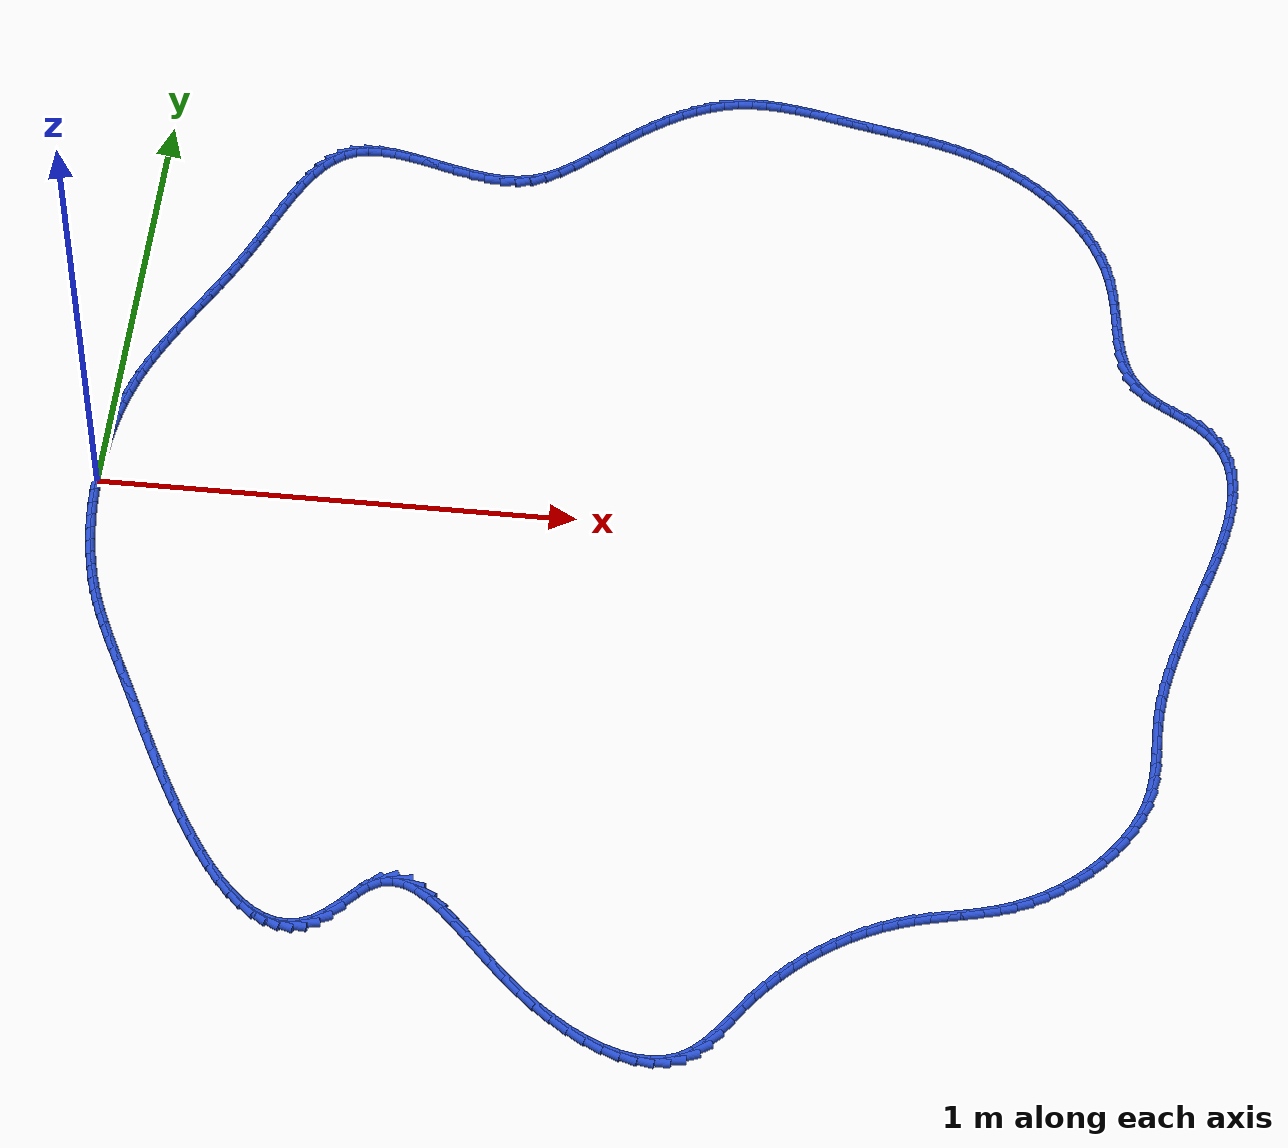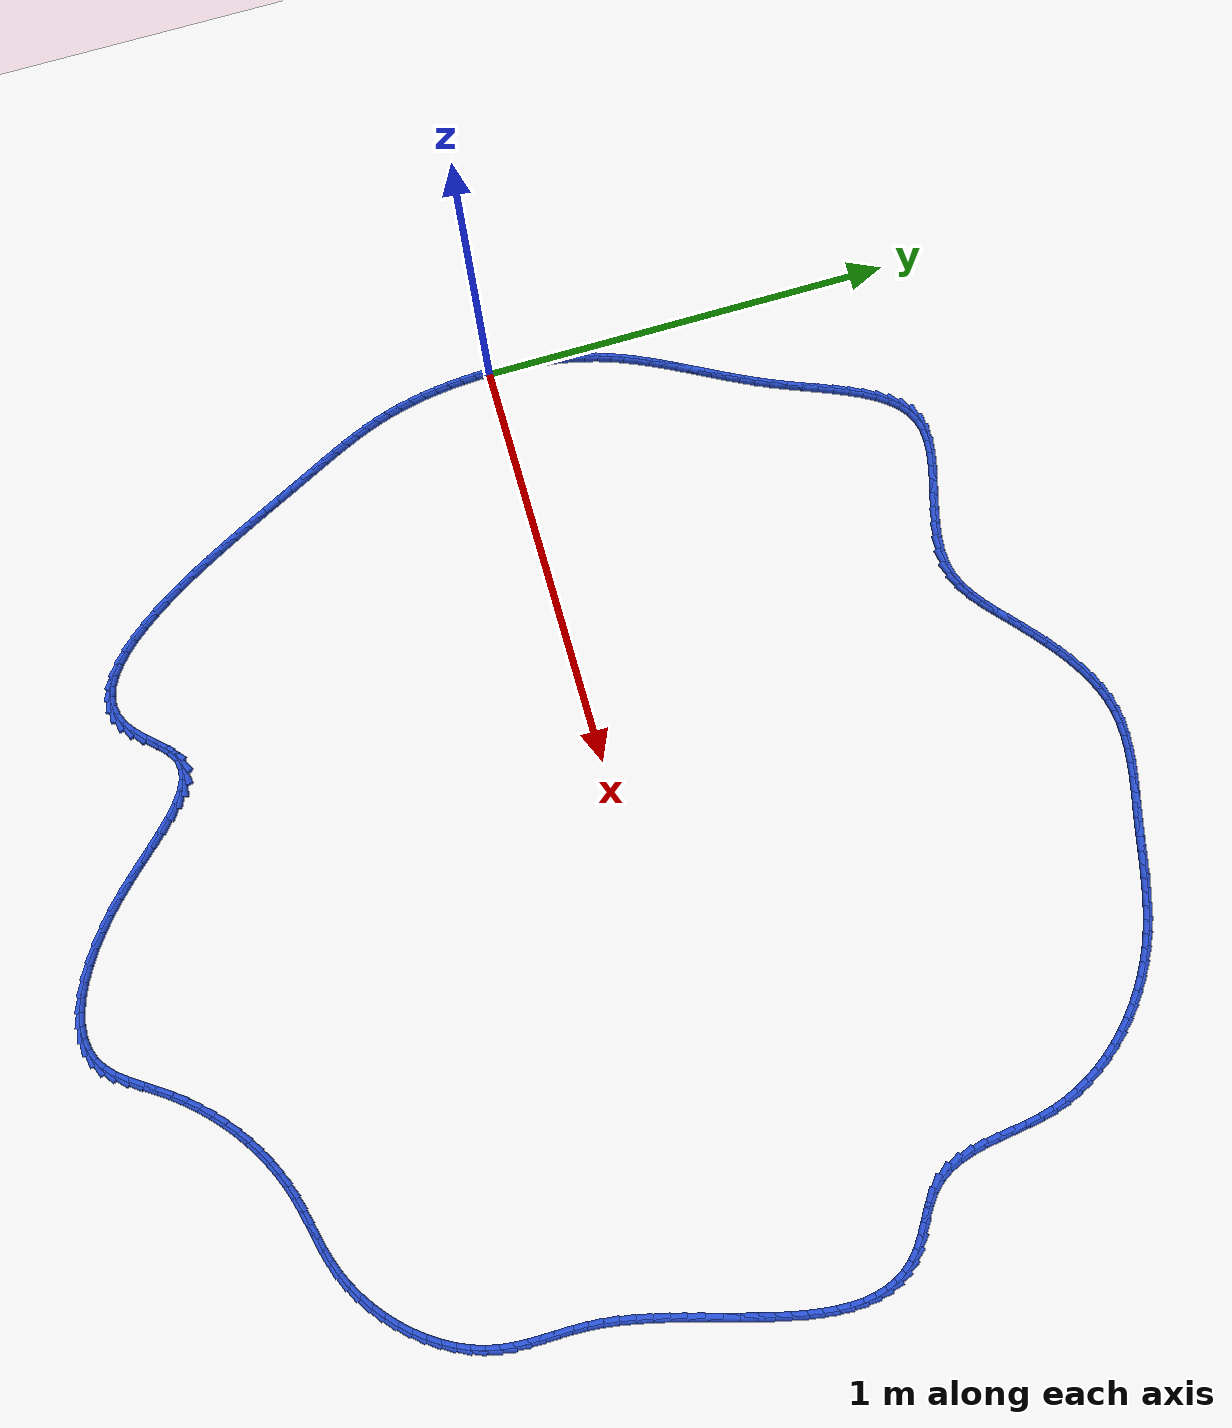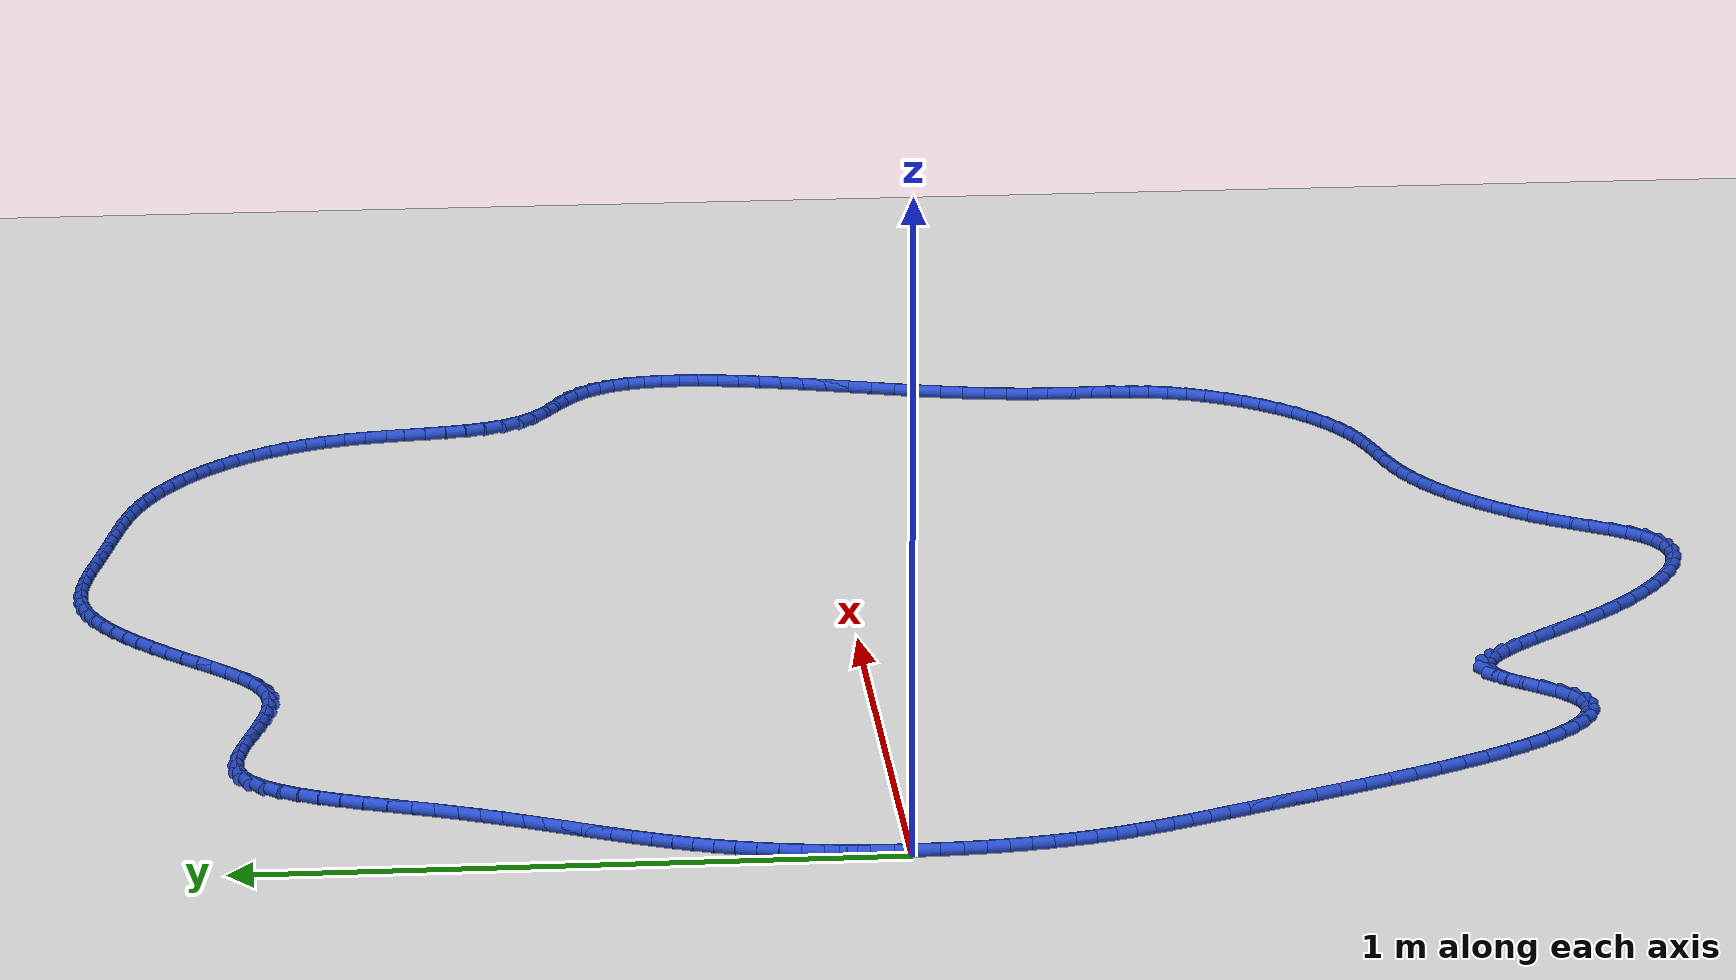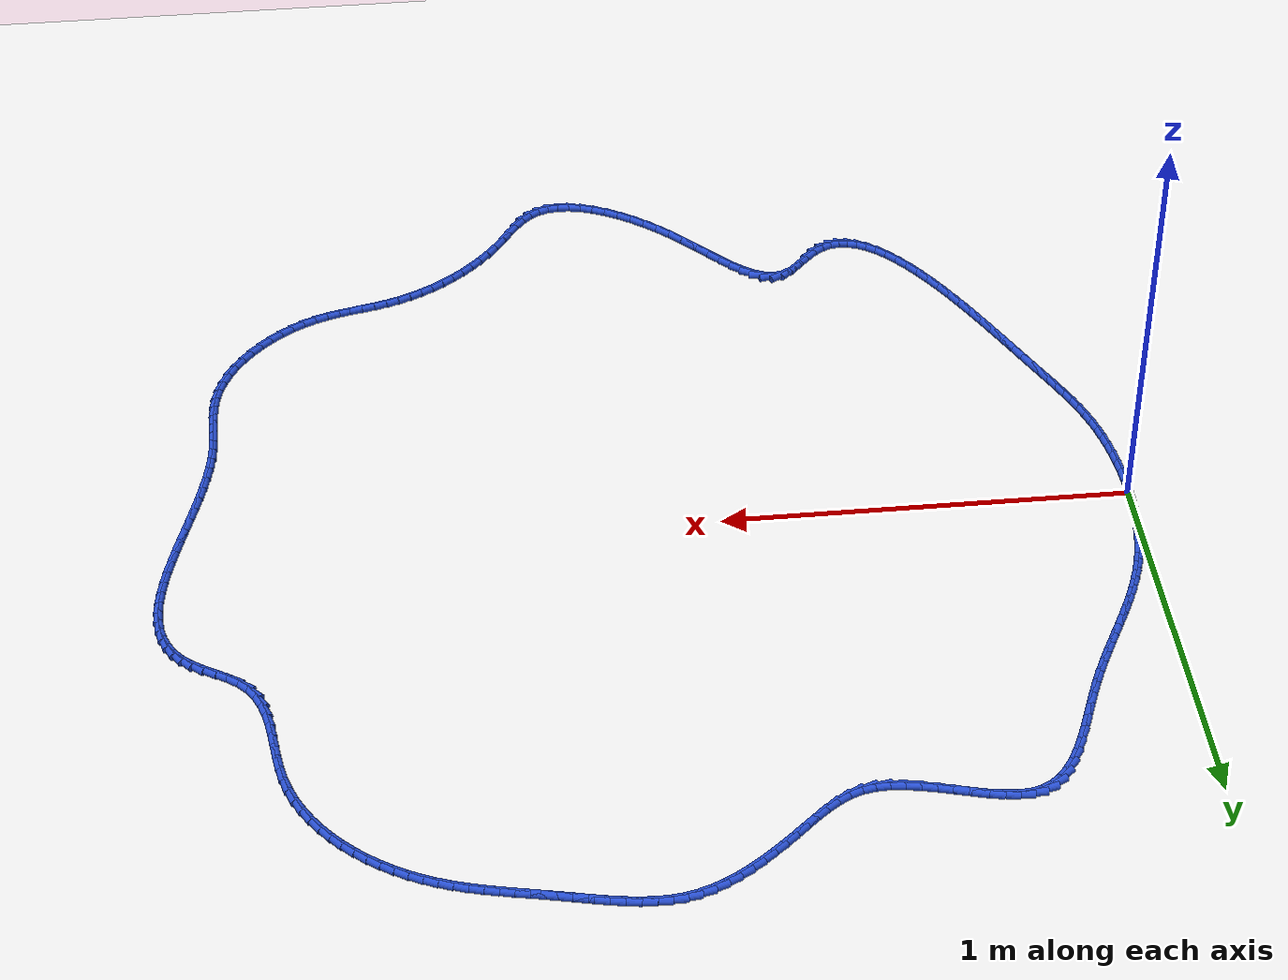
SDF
<sdf version="1.6">
 <world name="default">
  <light name="sun" type="directional">
   <pose>0 0 10 0 -0 0</pose>
   <diffuse>0.8 0.8 0.8 1</diffuse>
   <specular>0.2 0.2 0.2 1</specular>
   <attenuation>
    <range>1000</range>
    <constant>0.9</constant>
    <linear>0.01</linear>
    <quadratic>0.001</quadratic>
   </attenuation>
   <direction>-0.5 0.1 -0.9</direction>
  </light>
  <model name="ground_plane">
   <static>1</static>
   <link name="link">
    <collision name="collision">
     <geometry><plane><normal>0 0 1</normal><size>100 100</size></plane></geometry>
     <surface><friction><ode><mu>100</mu><mu2>50</mu2></ode></friction></surface>
    </collision>
    <visual name="visual">
     <cast_shadows>0</cast_shadows>
     <geometry><plane><normal>0 0 1</normal><size>100 100</size></plane></geometry>
     <material>
      <script><uri>file://media/materials/scripts/gazebo.material</uri><name>Gazebo/WhiteGlow</name></script>
     </material>
    </visual>
   </link>
  </model>
  <gravity>0 0 -9.8</gravity>
  <magnetic_field>6e-06 2.3e-05 -4.2e-05</magnetic_field>
  <atmosphere type="adiabatic"/>
  <physics name="default_physics" default="0" type="ode">
   <max_step_size>0.001</max_step_size>
   <real_time_factor>1</real_time_factor>
   <real_time_update_rate>1000</real_time_update_rate>
  </physics>
  <scene><ambient>0.4 0.4 0.4 1</ambient><background>0.7 0.7 0.7 1</background><shadows>1</shadows></scene>
  <spherical_coordinates>
   <surface_model>EARTH_WGS84</surface_model>
   <latitude_deg>0</latitude_deg>
   <longitude_deg>0</longitude_deg>
   <elevation>0</elevation>
   <heading_deg>0</heading_deg>
  </spherical_coordinates>
  <model name="line">
   <link name="link_0">
    <pose>1.5612511283791264e-17 6.938893903907228e-17 0.01 0 1.57 1.5590957902085196</pose>
    <collision name="collision">
     <geometry><cylinder><radius>0.01</radius><length>0.08</length></cylinder></geometry>
    </collision>
    <visual name="visual">
     <material>
      <script><name>Gazebo/Blue</name><uri>file://media/materials/scripts/gazebo.material</uri></script>
     </material>
     <geometry><cylinder><radius>0.01</radius><length>0.08</length></cylinder></geometry>
    </visual>
   </link>
   <link name="link_1">
    <pose>0.00039795358519194497 0.03401001499382369 0.01 0 1.57 1.527344254759994</pose>
    <collision name="collision">
     <geometry><cylinder><radius>0.01</radius><length>0.08</length></cylinder></geometry>
    </collision>
    <visual name="visual">
     <material>
      <script><name>Gazebo/Blue</name><uri>file://media/materials/scripts/gazebo.material</uri></script>
     </material>
     <geometry><cylinder><radius>0.01</radius><length>0.08</length></cylinder></geometry>
    </visual>
   </link>
   <link name="link_2">
    <pose>0.0018704710210854767 0.06787699775144895 0.01 0 1.57 1.4943016651344494</pose>
    <collision name="collision">
     <geometry><cylinder><radius>0.01</radius><length>0.08</length></cylinder></geometry>
    </collision>
    <visual name="visual">
     <material>
      <script><name>Gazebo/Blue</name><uri>file://media/materials/scripts/gazebo.material</uri></script>
     </material>
     <geometry><cylinder><radius>0.01</radius><length>0.08</length></cylinder></geometry>
    </visual>
   </link>
   <link name="link_3">
    <pose>0.004448175908305287 0.1015090854414555 0.01 0 1.57 1.4597558159385076</pose>
    <collision name="collision">
     <geometry><cylinder><radius>0.01</radius><length>0.08</length></cylinder></geometry>
    </collision>
    <visual name="visual">
     <material>
      <script><name>Gazebo/Blue</name><uri>file://media/materials/scripts/gazebo.material</uri></script>
     </material>
     <geometry><cylinder><radius>0.01</radius><length>0.08</length></cylinder></geometry>
    </visual>
   </link>
   <link name="link_4">
    <pose>0.00816169184747604 0.1348144152324228 0.01 0 1.57 1.4234845401696197</pose>
    <collision name="collision">
     <geometry><cylinder><radius>0.01</radius><length>0.08</length></cylinder></geometry>
    </collision>
    <visual name="visual">
     <material>
      <script><name>Gazebo/Blue</name><uri>file://media/materials/scripts/gazebo.material</uri></script>
     </material>
     <geometry><cylinder><radius>0.01</radius><length>0.08</length></cylinder></geometry>
    </visual>
   </link>
   <link name="link_5">
    <pose>0.013041642439222418 0.16770112429293058 0.01 0 1.57 1.3852554352615685</pose>
    <collision name="collision">
     <geometry><cylinder><radius>0.01</radius><length>0.08</length></cylinder></geometry>
    </collision>
    <visual name="visual">
     <material>
      <script><name>Gazebo/Blue</name><uri>file://media/materials/scripts/gazebo.material</uri></script>
     </material>
     <geometry><cylinder><radius>0.01</radius><length>0.08</length></cylinder></geometry>
    </visual>
   </link>
   <link name="link_6">
    <pose>0.019118651284169095 0.20007734979155828 0.01 0 1.57 1.344826626539135</pose>
    <collision name="collision">
     <geometry><cylinder><radius>0.01</radius><length>0.08</length></cylinder></geometry>
    </collision>
    <visual name="visual">
     <material>
      <script><name>Gazebo/Blue</name><uri>file://media/materials/scripts/gazebo.material</uri></script>
     </material>
     <geometry><cylinder><radius>0.01</radius><length>0.08</length></cylinder></geometry>
    </visual>
   </link>
   <link name="link_7">
    <pose>0.026423341982940725 0.2318512288968855 0.01 0 1.57 1.3019489680391543</pose>
    <collision name="collision">
     <geometry><cylinder><radius>0.01</radius><length>0.08</length></cylinder></geometry>
    </collision>
    <visual name="visual">
     <material>
      <script><name>Gazebo/Blue</name><uri>file://media/materials/scripts/gazebo.material</uri></script>
     </material>
     <geometry><cylinder><radius>0.01</radius><length>0.08</length></cylinder></geometry>
    </visual>
   </link>
   <link name="link_8">
    <pose>0.034986338136162004 0.2629308987774918 0.01 0 1.57 1.2569548308997691</pose>
    <collision name="collision">
     <geometry><cylinder><radius>0.01</radius><length>0.08</length></cylinder></geometry>
    </collision>
    <visual name="visual">
     <material>
      <script><name>Gazebo/Blue</name><uri>file://media/materials/scripts/gazebo.material</uri></script>
     </material>
     <geometry><cylinder><radius>0.01</radius><length>0.08</length></cylinder></geometry>
    </visual>
   </link>
   <link name="link_9">
    <pose>0.04482512598660589 0.2932443470038685 0.01 0 1.57 1.2145632126685058</pose>
    <collision name="collision">
     <geometry><cylinder><radius>0.01</radius><length>0.08</length></cylinder></geometry>
    </collision>
    <visual name="visual">
     <material>
      <script><name>Gazebo/Blue</name><uri>file://media/materials/scripts/gazebo.material</uri></script>
     </material>
     <geometry><cylinder><radius>0.01</radius><length>0.08</length></cylinder></geometry>
    </visual>
   </link>
   <link name="link_10">
    <pose>0.05585215579845866 0.32287826934443 0.01 0 1.57 1.1776106224616119</pose>
    <collision name="collision">
     <geometry><cylinder><radius>0.01</radius><length>0.08</length></cylinder></geometry>
    </collision>
    <visual name="visual">
     <material>
      <script><name>Gazebo/Blue</name><uri>file://media/materials/scripts/gazebo.material</uri></script>
     </material>
     <geometry><cylinder><radius>0.01</radius><length>0.08</length></cylinder></geometry>
    </visual>
   </link>
   <link name="link_11">
    <pose>0.06792950222542031 0.35199547855595215 0.01 0 1.57 1.1466214942020267</pose>
    <collision name="collision">
     <geometry><cylinder><radius>0.01</radius><length>0.08</length></cylinder></geometry>
    </collision>
    <visual name="visual">
     <material>
      <script><name>Gazebo/Blue</name><uri>file://media/materials/scripts/gazebo.material</uri></script>
     </material>
     <geometry><cylinder><radius>0.01</radius><length>0.08</length></cylinder></geometry>
    </visual>
   </link>
   <link name="link_12">
    <pose>0.0809189224088432 0.38075926715284397 0.01 0 1.57 1.1219149535525959</pose>
    <collision name="collision">
     <geometry><cylinder><radius>0.01</radius><length>0.08</length></cylinder></geometry>
    </collision>
    <visual name="visual">
     <material>
      <script><name>Gazebo/Blue</name><uri>file://media/materials/scripts/gazebo.material</uri></script>
     </material>
     <geometry><cylinder><radius>0.01</radius><length>0.08</length></cylinder></geometry>
    </visual>
   </link>
   <link name="link_13">
    <pose>0.09468217349007967 0.4093329276495145 0.01 0 1.57 1.1036399254134206</pose>
    <collision name="collision">
     <geometry><cylinder><radius>0.01</radius><length>0.08</length></cylinder></geometry>
    </collision>
    <visual name="visual">
     <material>
      <script><name>Gazebo/Blue</name><uri>file://media/materials/scripts/gazebo.material</uri></script>
     </material>
     <geometry><cylinder><radius>0.01</radius><length>0.08</length></cylinder></geometry>
    </visual>
   </link>
   <link name="link_14">
    <pose>0.1090810126104822 0.43787975256037287 0.01 0 1.57 1.0918019489527087</pose>
    <collision name="collision">
     <geometry><cylinder><radius>0.01</radius><length>0.08</length></cylinder></geometry>
    </collision>
    <visual name="visual">
     <material>
      <script><name>Gazebo/Blue</name><uri>file://media/materials/scripts/gazebo.material</uri></script>
     </material>
     <geometry><cylinder><radius>0.01</radius><length>0.08</length></cylinder></geometry>
    </visual>
   </link>
   <link name="link_15">
    <pose>0.12397719691140308 0.46656303439982805 0.01 0 1.57 1.0862897684399544</pose>
    <collision name="collision">
     <geometry><cylinder><radius>0.01</radius><length>0.08</length></cylinder></geometry>
    </collision>
    <visual name="visual">
     <material>
      <script><name>Gazebo/Blue</name><uri>file://media/materials/scripts/gazebo.material</uri></script>
     </material>
     <geometry><cylinder><radius>0.01</radius><length>0.08</length></cylinder></geometry>
    </visual>
   </link>
   <link name="link_16">
    <pose>0.13923248353419473 0.495546065682289 0.01 0 1.57 1.0868979768102938</pose>
    <collision name="collision">
     <geometry><cylinder><radius>0.01</radius><length>0.08</length></cylinder></geometry>
    </collision>
    <visual name="visual">
     <material>
      <script><name>Gazebo/Blue</name><uri>file://media/materials/scripts/gazebo.material</uri></script>
     </material>
     <geometry><cylinder><radius>0.01</radius><length>0.08</length></cylinder></geometry>
    </visual>
   </link>
   <link name="link_17">
    <pose>0.1547086296202096 0.5249921389221651 0.01 0 1.57 1.0933442014532393</pose>
    <collision name="collision">
     <geometry><cylinder><radius>0.01</radius><length>0.08</length></cylinder></geometry>
    </collision>
    <visual name="visual">
     <material>
      <script><name>Gazebo/Blue</name><uri>file://media/materials/scripts/gazebo.material</uri></script>
     </material>
     <geometry><cylinder><radius>0.01</radius><length>0.08</length></cylinder></geometry>
    </visual>
   </link>
   <link name="link_18">
    <pose>0.17026739231080001 0.5550645466338653 0.01 0 1.57 1.1052810080170552</pose>
    <collision name="collision">
     <geometry><cylinder><radius>0.01</radius><length>0.08</length></cylinder></geometry>
    </collision>
    <visual name="visual">
     <material>
      <script><name>Gazebo/Blue</name><uri>file://media/materials/scripts/gazebo.material</uri></script>
     </material>
     <geometry><cylinder><radius>0.01</radius><length>0.08</length></cylinder></geometry>
    </visual>
   </link>
   <link name="link_19">
    <pose>0.1857705287473183 0.5859265813317983 0.01 0 1.57 1.1223037779074598</pose>
    <collision name="collision">
     <geometry><cylinder><radius>0.01</radius><length>0.08</length></cylinder></geometry>
    </collision>
    <visual name="visual">
     <material>
      <script><name>Gazebo/Blue</name><uri>file://media/materials/scripts/gazebo.material</uri></script>
     </material>
     <geometry><cylinder><radius>0.01</radius><length>0.08</length></cylinder></geometry>
    </visual>
   </link>
   <link name="link_20">
    <pose>0.20107979607111703 0.6177415355303737 0.01 0 1.57 1.1439563611687862</pose>
    <collision name="collision">
     <geometry><cylinder><radius>0.01</radius><length>0.08</length></cylinder></geometry>
    </collision>
    <visual name="visual">
     <material>
      <script><name>Gazebo/Blue</name><uri>file://media/materials/scripts/gazebo.material</uri></script>
     </material>
     <geometry><cylinder><radius>0.01</radius><length>0.08</length></cylinder></geometry>
    </visual>
   </link>
   <link name="link_21">
    <pose>0.21605695142354844 0.6506727017440003 0.01 0 1.57 1.169486346922027</pose>
    <collision name="collision">
     <geometry><cylinder><radius>0.01</radius><length>0.08</length></cylinder></geometry>
    </collision>
    <visual name="visual">
     <material>
      <script><name>Gazebo/Blue</name><uri>file://media/materials/scripts/gazebo.material</uri></script>
     </material>
     <geometry><cylinder><radius>0.01</radius><length>0.08</length></cylinder></geometry>
    </visual>
   </link>
   <link name="link_22">
    <pose>0.2305692575888098 0.6848725581302799 0.01 0 1.57 1.1900381478327313</pose>
    <collision name="collision">
     <geometry><cylinder><radius>0.01</radius><length>0.08</length></cylinder></geometry>
    </collision>
    <visual name="visual">
     <material>
      <script><name>Gazebo/Blue</name><uri>file://media/materials/scripts/gazebo.material</uri></script>
     </material>
     <geometry><cylinder><radius>0.01</radius><length>0.08</length></cylinder></geometry>
    </visual>
   </link>
   <link name="link_23">
    <pose>0.24467661139991284 0.72011520499053 0.01 0 1.57 1.1960094326079989</pose>
    <collision name="collision">
     <geometry><cylinder><radius>0.01</radius><length>0.08</length></cylinder></geometry>
    </collision>
    <visual name="visual">
     <material>
      <script><name>Gazebo/Blue</name><uri>file://media/materials/scripts/gazebo.material</uri></script>
     </material>
     <geometry><cylinder><radius>0.01</radius><length>0.08</length></cylinder></geometry>
    </visual>
   </link>
   <link name="link_24">
    <pose>0.2586774283061442 0.7557062368594836 0.01 0 1.57 1.1873279173007258</pose>
    <collision name="collision">
     <geometry><cylinder><radius>0.01</radius><length>0.08</length></cylinder></geometry>
    </collision>
    <visual name="visual">
     <material>
      <script><name>Gazebo/Blue</name><uri>file://media/materials/scripts/gazebo.material</uri></script>
     </material>
     <geometry><cylinder><radius>0.01</radius><length>0.08</length></cylinder></geometry>
    </visual>
   </link>
   <link name="link_25">
    <pose>0.27288493783246437 0.7909221499985897 0.01 0 1.57 1.1632892073238223</pose>
    <collision name="collision">
     <geometry><cylinder><radius>0.01</radius><length>0.08</length></cylinder></geometry>
    </collision>
    <visual name="visual">
     <material>
      <script><name>Gazebo/Blue</name><uri>file://media/materials/scripts/gazebo.material</uri></script>
     </material>
     <geometry><cylinder><radius>0.01</radius><length>0.08</length></cylinder></geometry>
    </visual>
   </link>
   <link name="link_26">
    <pose>0.28761236950383434 0.8250394406692969 0.01 0 1.57 1.1217950118944597</pose>
    <collision name="collision">
     <geometry><cylinder><radius>0.01</radius><length>0.08</length></cylinder></geometry>
    </collision>
    <visual name="visual">
     <material>
      <script><name>Gazebo/Blue</name><uri>file://media/materials/scripts/gazebo.material</uri></script>
     </material>
     <geometry><cylinder><radius>0.01</radius><length>0.08</length></cylinder></geometry>
    </visual>
   </link>
   <link name="link_27">
    <pose>0.30317295284521445 0.8573346051330537 0.01 0 1.57 1.059100367536076</pose>
    <collision name="collision">
     <geometry><cylinder><radius>0.01</radius><length>0.08</length></cylinder></geometry>
    </collision>
    <visual name="visual">
     <material>
      <script><name>Gazebo/Blue</name><uri>file://media/materials/scripts/gazebo.material</uri></script>
     </material>
     <geometry><cylinder><radius>0.01</radius><length>0.08</length></cylinder></geometry>
    </visual>
   </link>
   <link name="link_28">
    <pose>0.31987991738156546 0.8870841396513087 0.01 0 1.57 0.9695020620723478</pose>
    <collision name="collision">
     <geometry><cylinder><radius>0.01</radius><length>0.08</length></cylinder></geometry>
    </collision>
    <visual name="visual">
     <material>
      <script><name>Gazebo/Blue</name><uri>file://media/materials/scripts/gazebo.material</uri></script>
     </material>
     <geometry><cylinder><radius>0.01</radius><length>0.08</length></cylinder></geometry>
    </visual>
   </link>
   <link name="link_29">
    <pose>0.33804649263784775 0.9135645404855103 0.01 0 1.57 0.8453901318244618</pose>
    <collision name="collision">
     <geometry><cylinder><radius>0.01</radius><length>0.08</length></cylinder></geometry>
    </collision>
    <visual name="visual">
     <material>
      <script><name>Gazebo/Blue</name><uri>file://media/materials/scripts/gazebo.material</uri></script>
     </material>
     <geometry><cylinder><radius>0.01</radius><length>0.08</length></cylinder></geometry>
    </visual>
   </link>
   <link name="link_30">
    <pose>0.35798590813902226 0.9360523038971075 0.01 0 1.57 0.678913722099576</pose>
    <collision name="collision">
     <geometry><cylinder><radius>0.01</radius><length>0.08</length></cylinder></geometry>
    </collision>
    <visual name="visual">
     <material>
      <script><name>Gazebo/Blue</name><uri>file://media/materials/scripts/gazebo.material</uri></script>
     </material>
     <geometry><cylinder><radius>0.01</radius><length>0.08</length></cylinder></geometry>
    </visual>
   </link>
   <link name="link_31">
    <pose>0.3800113934100494 0.9538239261475485 0.01 0 1.57 0.4675567765697216</pose>
    <collision name="collision">
     <geometry><cylinder><radius>0.01</radius><length>0.08</length></cylinder></geometry>
    </collision>
    <visual name="visual">
     <material>
      <script><name>Gazebo/Blue</name><uri>file://media/materials/scripts/gazebo.material</uri></script>
     </material>
     <geometry><cylinder><radius>0.01</radius><length>0.08</length></cylinder></geometry>
    </visual>
   </link>
   <link name="link_32">
    <pose>0.40443617797589004 0.9661559034982821 0.01 0 1.57 0.23184507173724725</pose>
    <collision name="collision">
     <geometry><cylinder><radius>0.01</radius><length>0.08</length></cylinder></geometry>
    </collision>
    <visual name="visual">
     <material>
      <script><name>Gazebo/Blue</name><uri>file://media/materials/scripts/gazebo.material</uri></script>
     </material>
     <geometry><cylinder><radius>0.01</radius><length>0.08</length></cylinder></geometry>
    </visual>
   </link>
   <link name="link_33">
    <pose>0.43148621310586693 0.9725421579244949 0.01 0 1.57 0.03751136515576781</pose>
    <collision name="collision">
     <geometry><cylinder><radius>0.01</radius><length>0.08</length></cylinder></geometry>
    </collision>
    <visual name="visual">
     <material>
      <script><name>Gazebo/Blue</name><uri>file://media/materials/scripts/gazebo.material</uri></script>
     </material>
     <geometry><cylinder><radius>0.01</radius><length>0.08</length></cylinder></geometry>
    </visual>
   </link>
   <link name="link_34">
    <pose>0.46091775986625194 0.9736466935356731 0.01 0 1.57 -0.09904123851204222</pose>
    <collision name="collision">
     <geometry><cylinder><radius>0.01</radius><length>0.08</length></cylinder></geometry>
    </collision>
    <visual name="visual">
     <material>
      <script><name>Gazebo/Blue</name><uri>file://media/materials/scripts/gazebo.material</uri></script>
     </material>
     <geometry><cylinder><radius>0.01</radius><length>0.08</length></cylinder></geometry>
    </visual>
   </link>
   <link name="link_35">
    <pose>0.4923297714011501 0.9705253965544802 0.01 0 1.57 -0.18842335032717966</pose>
    <collision name="collision">
     <geometry><cylinder><radius>0.01</radius><length>0.08</length></cylinder></geometry>
    </collision>
    <visual name="visual">
     <material>
      <script><name>Gazebo/Blue</name><uri>file://media/materials/scripts/gazebo.material</uri></script>
     </material>
     <geometry><cylinder><radius>0.01</radius><length>0.08</length></cylinder></geometry>
    </visual>
   </link>
   <link name="link_36">
    <pose>0.5253210876063509 0.9642344353253495 0.01 0 1.57 -0.24117647925139293</pose>
    <collision name="collision">
     <geometry><cylinder><radius>0.01</radius><length>0.08</length></cylinder></geometry>
    </collision>
    <visual name="visual">
     <material>
      <script><name>Gazebo/Blue</name><uri>file://media/materials/scripts/gazebo.material</uri></script>
     </material>
     <geometry><cylinder><radius>0.01</radius><length>0.08</length></cylinder></geometry>
    </visual>
   </link>
   <link name="link_37">
    <pose>0.5594905483776438 0.9558299781927136 0.01 0 1.57 -0.2644116660805654</pose>
    <collision name="collision">
     <geometry><cylinder><radius>0.01</radius><length>0.08</length></cylinder></geometry>
    </collision>
    <visual name="visual">
     <material>
      <script><name>Gazebo/Blue</name><uri>file://media/materials/scripts/gazebo.material</uri></script>
     </material>
     <geometry><cylinder><radius>0.01</radius><length>0.08</length></cylinder></geometry>
    </visual>
   </link>
   <link name="link_38">
    <pose>0.5944369936108177 0.9463681935010058 0.01 0 1.57 -0.261756339791435</pose>
    <collision name="collision">
     <geometry><cylinder><radius>0.01</radius><length>0.08</length></cylinder></geometry>
    </collision>
    <visual name="visual">
     <material>
      <script><name>Gazebo/Blue</name><uri>file://media/materials/scripts/gazebo.material</uri></script>
     </material>
     <geometry><cylinder><radius>0.01</radius><length>0.08</length></cylinder></geometry>
    </visual>
   </link>
   <link name="link_39">
    <pose>0.6297592632016628 0.9369052495946587 0.01 0 1.57 -0.2338478197965022</pose>
    <collision name="collision">
     <geometry><cylinder><radius>0.01</radius><length>0.08</length></cylinder></geometry>
    </collision>
    <visual name="visual">
     <material>
      <script><name>Gazebo/Blue</name><uri>file://media/materials/scripts/gazebo.material</uri></script>
     </material>
     <geometry><cylinder><radius>0.01</radius><length>0.08</length></cylinder></geometry>
    </visual>
   </link>
   <link name="link_40">
    <pose>0.6650561970459677 0.9284973148181053 0.01 0 1.57 -0.17865061356322054</pose>
    <collision name="collision">
     <geometry><cylinder><radius>0.01</radius><length>0.08</length></cylinder></geometry>
    </collision>
    <visual name="visual">
     <material>
      <script><name>Gazebo/Blue</name><uri>file://media/materials/scripts/gazebo.material</uri></script>
     </material>
     <geometry><cylinder><radius>0.01</radius><length>0.08</length></cylinder></geometry>
    </visual>
   </link>
   <link name="link_41">
    <pose>0.6999266350395222 0.9222005575157787 0.01 0 1.57 -0.09166821383920071</pose>
    <collision name="collision">
     <geometry><cylinder><radius>0.01</radius><length>0.08</length></cylinder></geometry>
    </collision>
    <visual name="visual">
     <material>
      <script><name>Gazebo/Blue</name><uri>file://media/materials/scripts/gazebo.material</uri></script>
     </material>
     <geometry><cylinder><radius>0.01</radius><length>0.08</length></cylinder></geometry>
    </visual>
   </link>
   <link name="link_42">
    <pose>0.7339694170781157 0.9190711460321118 0.01 0 1.57 0.033330244262174444</pose>
    <collision name="collision">
     <geometry><cylinder><radius>0.01</radius><length>0.08</length></cylinder></geometry>
    </collision>
    <visual name="visual">
     <material>
      <script><name>Gazebo/Blue</name><uri>file://media/materials/scripts/gazebo.material</uri></script>
     </material>
     <geometry><cylinder><radius>0.01</radius><length>0.08</length></cylinder></geometry>
    </visual>
   </link>
   <link name="link_43">
    <pose>0.7667833830575372 0.9201652487115375 0.01 0 1.57 0.20135702583722084</pose>
    <collision name="collision">
     <geometry><cylinder><radius>0.01</radius><length>0.08</length></cylinder></geometry>
    </collision>
    <visual name="visual">
     <material>
      <script><name>Gazebo/Blue</name><uri>file://media/materials/scripts/gazebo.material</uri></script>
     </material>
     <geometry><cylinder><radius>0.01</radius><length>0.08</length></cylinder></geometry>
    </visual>
   </link>
   <link name="link_44">
    <pose>0.7979702252729663 0.9265312071475406 0.01 0 1.57 0.38580186840207403</pose>
    <collision name="collision">
     <geometry><cylinder><radius>0.01</radius><length>0.08</length></cylinder></geometry>
    </collision>
    <visual name="visual">
     <material>
      <script><name>Gazebo/Blue</name><uri>file://media/materials/scripts/gazebo.material</uri></script>
     </material>
     <geometry><cylinder><radius>0.01</radius><length>0.08</length></cylinder></geometry>
    </visual>
   </link>
   <link name="link_45">
    <pose>0.8273989559864888 0.9384838587785242 0.01 0 1.57 0.5330181427562914</pose>
    <collision name="collision">
     <geometry><cylinder><radius>0.01</radius><length>0.08</length></cylinder></geometry>
    </collision>
    <visual name="visual">
     <material>
      <script><name>Gazebo/Blue</name><uri>file://media/materials/scripts/gazebo.material</uri></script>
     </material>
     <geometry><cylinder><radius>0.01</radius><length>0.08</length></cylinder></geometry>
    </visual>
   </link>
   <link name="link_46">
    <pose>0.8554204237606388 0.9550159215897921 0.01 0 1.57 0.6364524290097345</pose>
    <collision name="collision">
     <geometry><cylinder><radius>0.01</radius><length>0.08</length></cylinder></geometry>
    </collision>
    <visual name="visual">
     <material>
      <script><name>Gazebo/Blue</name><uri>file://media/materials/scripts/gazebo.material</uri></script>
     </material>
     <geometry><cylinder><radius>0.01</radius><length>0.08</length></cylinder></geometry>
    </visual>
   </link>
   <link name="link_47">
    <pose>0.8824359589961419 0.9749815955258975 0.01 0 1.57 0.7001741330436244</pose>
    <collision name="collision">
     <geometry><cylinder><radius>0.01</radius><length>0.08</length></cylinder></geometry>
    </collision>
    <visual name="visual">
     <material>
      <script><name>Gazebo/Blue</name><uri>file://media/materials/scripts/gazebo.material</uri></script>
     </material>
     <geometry><cylinder><radius>0.01</radius><length>0.08</length></cylinder></geometry>
    </visual>
   </link>
   <link name="link_48">
    <pose>0.9088468920937238 0.9972350805313942 0.01 0 1.57 0.7287655133686541</pose>
    <collision name="collision">
     <geometry><cylinder><radius>0.01</radius><length>0.08</length></cylinder></geometry>
    </collision>
    <visual name="visual">
     <material>
      <script><name>Gazebo/Blue</name><uri>file://media/materials/scripts/gazebo.material</uri></script>
     </material>
     <geometry><cylinder><radius>0.01</radius><length>0.08</length></cylinder></geometry>
    </visual>
   </link>
   <link name="link_49">
    <pose>0.9350545534541106 1.0206305765508354 0.01 0 1.57 0.7279716062282392</pose>
    <collision name="collision">
     <geometry><cylinder><radius>0.01</radius><length>0.08</length></cylinder></geometry>
    </collision>
    <visual name="visual">
     <material>
      <script><name>Gazebo/Blue</name><uri>file://media/materials/scripts/gazebo.material</uri></script>
     </material>
     <geometry><cylinder><radius>0.01</radius><length>0.08</length></cylinder></geometry>
    </visual>
   </link>
   <link name="link_50">
    <pose>0.9614150575036575 1.0441249360684821 0.01 0 1.57 0.7137939574656241</pose>
    <collision name="collision">
     <geometry><cylinder><radius>0.01</radius><length>0.08</length></cylinder></geometry>
    </collision>
    <visual name="visual">
     <material>
      <script><name>Gazebo/Blue</name><uri>file://media/materials/scripts/gazebo.material</uri></script>
     </material>
     <geometry><cylinder><radius>0.01</radius><length>0.08</length></cylinder></geometry>
    </visual>
   </link>
   <link name="link_51">
    <pose>0.9880540544326912 1.0671982279643346 0.01 0 1.57 0.6908669163755314</pose>
    <collision name="collision">
     <geometry><cylinder><radius>0.01</radius><length>0.08</length></cylinder></geometry>
    </collision>
    <visual name="visual">
     <material>
      <script><name>Gazebo/Blue</name><uri>file://media/materials/scripts/gazebo.material</uri></script>
     </material>
     <geometry><cylinder><radius>0.01</radius><length>0.08</length></cylinder></geometry>
    </visual>
   </link>
   <link name="link_52">
    <pose>1.0150239545582729 1.0894967955181696 0.01 0 1.57 0.6586596648118807</pose>
    <collision name="collision">
     <geometry><cylinder><radius>0.01</radius><length>0.08</length></cylinder></geometry>
    </collision>
    <visual name="visual">
     <material>
      <script><name>Gazebo/Blue</name><uri>file://media/materials/scripts/gazebo.material</uri></script>
     </material>
     <geometry><cylinder><radius>0.01</radius><length>0.08</length></cylinder></geometry>
    </visual>
   </link>
   <link name="link_53">
    <pose>1.042377137877882 1.1106670508434446 0.01 0 1.57 0.6164068920458804</pose>
    <collision name="collision">
     <geometry><cylinder><radius>0.01</radius><length>0.08</length></cylinder></geometry>
    </collision>
    <visual name="visual">
     <material>
      <script><name>Gazebo/Blue</name><uri>file://media/materials/scripts/gazebo.material</uri></script>
     </material>
     <geometry><cylinder><radius>0.01</radius><length>0.08</length></cylinder></geometry>
    </visual>
   </link>
   <link name="link_54">
    <pose>1.070165984388998 1.130355406053617 0.01 0 1.57 0.5631589758289156</pose>
    <collision name="collision">
     <geometry><cylinder><radius>0.01</radius><length>0.08</length></cylinder></geometry>
    </collision>
    <visual name="visual">
     <material>
      <script><name>Gazebo/Blue</name><uri>file://media/materials/scripts/gazebo.material</uri></script>
     </material>
     <geometry><cylinder><radius>0.01</radius><length>0.08</length></cylinder></geometry>
    </visual>
   </link>
   <link name="link_55">
    <pose>1.0984428740891006 1.1482082732621441 0.01 0 1.57 0.49788148652644393</pose>
    <collision name="collision">
     <geometry><cylinder><radius>0.01</radius><length>0.08</length></cylinder></geometry>
    </collision>
    <visual name="visual">
     <material>
      <script><name>Gazebo/Blue</name><uri>file://media/materials/scripts/gazebo.material</uri></script>
     </material>
     <geometry><cylinder><radius>0.01</radius><length>0.08</length></cylinder></geometry>
    </visual>
   </link>
   <link name="link_56">
    <pose>1.1272601869756693 1.1638720645824843 0.01 0 1.57 0.41964210380648614</pose>
    <collision name="collision">
     <geometry><cylinder><radius>0.01</radius><length>0.08</length></cylinder></geometry>
    </collision>
    <visual name="visual">
     <material>
      <script><name>Gazebo/Blue</name><uri>file://media/materials/scripts/gazebo.material</uri></script>
     </material>
     <geometry><cylinder><radius>0.01</radius><length>0.08</length></cylinder></geometry>
    </visual>
   </link>
   <link name="link_57">
    <pose>1.1566703030461838 1.1769931921280947 0.01 0 1.57 0.3279196526299374</pose>
    <collision name="collision">
     <geometry><cylinder><radius>0.01</radius><length>0.08</length></cylinder></geometry>
    </collision>
    <visual name="visual">
     <material>
      <script><name>Gazebo/Blue</name><uri>file://media/materials/scripts/gazebo.material</uri></script>
     </material>
     <geometry><cylinder><radius>0.01</radius><length>0.08</length></cylinder></geometry>
    </visual>
   </link>
   <link name="link_58">
    <pose>1.1867256022981238 1.1872180680124333 0.01 0 1.57 0.22303592653227677</pose>
    <collision name="collision">
     <geometry><cylinder><radius>0.01</radius><length>0.08</length></cylinder></geometry>
    </collision>
    <visual name="visual">
     <material>
      <script><name>Gazebo/Blue</name><uri>file://media/materials/scripts/gazebo.material</uri></script>
     </material>
     <geometry><cylinder><radius>0.01</radius><length>0.08</length></cylinder></geometry>
    </visual>
   </link>
   <link name="link_59">
    <pose>1.2174784647289691 1.1941931043489578 0.01 0 1.57 0.11048410661142259</pose>
    <collision name="collision">
     <geometry><cylinder><radius>0.01</radius><length>0.08</length></cylinder></geometry>
    </collision>
    <visual name="visual">
     <material>
      <script><name>Gazebo/Blue</name><uri>file://media/materials/scripts/gazebo.material</uri></script>
     </material>
     <geometry><cylinder><radius>0.01</radius><length>0.08</length></cylinder></geometry>
    </visual>
   </link>
   <link name="link_60">
    <pose>1.2489569885513387 1.197685201545745 0.01 0 1.57 0.010984286786511463</pose>
    <collision name="collision">
     <geometry><cylinder><radius>0.01</radius><length>0.08</length></cylinder></geometry>
    </collision>
    <visual name="visual">
     <material>
      <script><name>Gazebo/Blue</name><uri>file://media/materials/scripts/gazebo.material</uri></script>
     </material>
     <geometry><cylinder><radius>0.01</radius><length>0.08</length></cylinder></geometry>
    </visual>
   </link>
   <link name="link_61">
    <pose>1.2810730451032468 1.1980379877098966 0.01 0 1.57 -0.06947088128762369</pose>
    <collision name="collision">
     <geometry><cylinder><radius>0.01</radius><length>0.08</length></cylinder></geometry>
    </collision>
    <visual name="visual">
     <material>
      <script><name>Gazebo/Blue</name><uri>file://media/materials/scripts/gazebo.material</uri></script>
     </material>
     <geometry><cylinder><radius>0.01</radius><length>0.08</length></cylinder></geometry>
    </visual>
   </link>
   <link name="link_62">
    <pose>1.31370377080805 1.19576744856781 0.01 0 1.57 -0.13180299623149003</pose>
    <collision name="collision">
     <geometry><cylinder><radius>0.01</radius><length>0.08</length></cylinder></geometry>
    </collision>
    <visual name="visual">
     <material>
      <script><name>Gazebo/Blue</name><uri>file://media/materials/scripts/gazebo.material</uri></script>
     </material>
     <geometry><cylinder><radius>0.01</radius><length>0.08</length></cylinder></geometry>
    </visual>
   </link>
   <link name="link_63">
    <pose>1.3467262958686452 1.1913896007123346 0.01 0 1.57 -0.1774143047019592</pose>
    <collision name="collision">
     <geometry><cylinder><radius>0.01</radius><length>0.08</length></cylinder></geometry>
    </collision>
    <visual name="visual">
     <material>
      <script><name>Gazebo/Blue</name><uri>file://media/materials/scripts/gazebo.material</uri></script>
     </material>
     <geometry><cylinder><radius>0.01</radius><length>0.08</length></cylinder></geometry>
    </visual>
   </link>
   <link name="link_64">
    <pose>1.3800177504879305 1.1854204607363203 0.01 0 1.57 -0.2076376558232692</pose>
    <collision name="collision">
     <geometry><cylinder><radius>0.01</radius><length>0.08</length></cylinder></geometry>
    </collision>
    <visual name="visual">
     <material>
      <script><name>Gazebo/Blue</name><uri>file://media/materials/scripts/gazebo.material</uri></script>
     </material>
     <geometry><cylinder><radius>0.01</radius><length>0.08</length></cylinder></geometry>
    </visual>
   </link>
   <link name="link_65">
    <pose>1.4134552648688032 1.178376045232617 0.01 0 1.57 -0.22344729937029575</pose>
    <collision name="collision">
     <geometry><cylinder><radius>0.01</radius><length>0.08</length></cylinder></geometry>
    </collision>
    <visual name="visual">
     <material>
      <script><name>Gazebo/Blue</name><uri>file://media/materials/scripts/gazebo.material</uri></script>
     </material>
     <geometry><cylinder><radius>0.01</radius><length>0.08</length></cylinder></geometry>
    </visual>
   </link>
   <link name="link_66">
    <pose>1.4469159692141609 1.1707723707940743 0.01 0 1.57 -0.2253246809924111</pose>
    <collision name="collision">
     <geometry><cylinder><radius>0.01</radius><length>0.08</length></cylinder></geometry>
    </collision>
    <visual name="visual">
     <material>
      <script><name>Gazebo/Blue</name><uri>file://media/materials/scripts/gazebo.material</uri></script>
     </material>
     <geometry><cylinder><radius>0.01</radius><length>0.08</length></cylinder></geometry>
    </visual>
   </link>
   <link name="link_67">
    <pose>1.480276993726901 1.1631254540135423 0.01 0 1.57 -0.21560855269663176</pose>
    <collision name="collision">
     <geometry><cylinder><radius>0.01</radius><length>0.08</length></cylinder></geometry>
    </collision>
    <visual name="visual">
     <material>
      <script><name>Gazebo/Blue</name><uri>file://media/materials/scripts/gazebo.material</uri></script>
     </material>
     <geometry><cylinder><radius>0.01</radius><length>0.08</length></cylinder></geometry>
    </visual>
   </link>
   <link name="link_68">
    <pose>1.5134262525850586 1.1558653396549476 0.01 0 1.57 -0.20876481389615256</pose>
    <collision name="collision">
     <geometry><cylinder><radius>0.01</radius><length>0.08</length></cylinder></geometry>
    </collision>
    <visual name="visual">
     <material>
      <script><name>Gazebo/Blue</name><uri>file://media/materials/scripts/gazebo.material</uri></script>
     </material>
     <geometry><cylinder><radius>0.01</radius><length>0.08</length></cylinder></geometry>
    </visual>
   </link>
   <link name="link_69">
    <pose>1.5463174875717518 1.148897282733533 0.01 0 1.57 -0.21052108686653578</pose>
    <collision name="collision">
     <geometry><cylinder><radius>0.01</radius><length>0.08</length></cylinder></geometry>
    </collision>
    <visual name="visual">
     <material>
      <script><name>Gazebo/Blue</name><uri>file://media/materials/scripts/gazebo.material</uri></script>
     </material>
     <geometry><cylinder><radius>0.01</radius><length>0.08</length></cylinder></geometry>
    </visual>
   </link>
   <link name="link_70">
    <pose>1.5789292741945764 1.1419285592553978 0.01 0 1.57 -0.22109387741301262</pose>
    <collision name="collision">
     <geometry><cylinder><radius>0.01</radius><length>0.08</length></cylinder></geometry>
    </collision>
    <visual name="visual">
     <material>
      <script><name>Gazebo/Blue</name><uri>file://media/materials/scripts/gazebo.material</uri></script>
     </material>
     <geometry><cylinder><radius>0.01</radius><length>0.08</length></cylinder></geometry>
    </visual>
   </link>
   <link name="link_71">
    <pose>1.6112402337181555 1.1346660804432311 0.01 0 1.57 -0.2406234395353036</pose>
    <collision name="collision">
     <geometry><cylinder><radius>0.01</radius><length>0.08</length></cylinder></geometry>
    </collision>
    <visual name="visual">
     <material>
      <script><name>Gazebo/Blue</name><uri>file://media/materials/scripts/gazebo.material</uri></script>
     </material>
     <geometry><cylinder><radius>0.01</radius><length>0.08</length></cylinder></geometry>
    </visual>
   </link>
   <link name="link_72">
    <pose>1.6432289874071124 1.1268167575197203 0.01 0 1.57 -0.26915439524321966</pose>
    <collision name="collision">
     <geometry><cylinder><radius>0.01</radius><length>0.08</length></cylinder></geometry>
    </collision>
    <visual name="visual">
     <material>
      <script><name>Gazebo/Blue</name><uri>file://media/materials/scripts/gazebo.material</uri></script>
     </material>
     <geometry><cylinder><radius>0.01</radius><length>0.08</length></cylinder></geometry>
    </visual>
   </link>
   <link name="link_73">
    <pose>1.6748741565260692 1.1180875017075547 0.01 0 1.57 -0.3065856337871052</pose>
    <collision name="collision">
     <geometry><cylinder><radius>0.01</radius><length>0.08</length></cylinder></geometry>
    </collision>
    <visual name="visual">
     <material>
      <script><name>Gazebo/Blue</name><uri>file://media/materials/scripts/gazebo.material</uri></script>
     </material>
     <geometry><cylinder><radius>0.01</radius><length>0.08</length></cylinder></geometry>
    </visual>
   </link>
   <link name="link_74">
    <pose>1.7061543623396493 1.1081852242294221 0.01 0 1.57 -0.35260381337323</pose>
    <collision name="collision">
     <geometry><cylinder><radius>0.01</radius><length>0.08</length></cylinder></geometry>
    </collision>
    <visual name="visual">
     <material>
      <script><name>Gazebo/Blue</name><uri>file://media/materials/scripts/gazebo.material</uri></script>
     </material>
     <geometry><cylinder><radius>0.01</radius><length>0.08</length></cylinder></geometry>
    </visual>
   </link>
   <link name="link_75">
    <pose>1.7370482261124753 1.0968168363080113 0.01 0 1.57 -0.4064503517024111</pose>
    <collision name="collision">
     <geometry><cylinder><radius>0.01</radius><length>0.08</length></cylinder></geometry>
    </collision>
    <visual name="visual">
     <material>
      <script><name>Gazebo/Blue</name><uri>file://media/materials/scripts/gazebo.material</uri></script>
     </material>
     <geometry><cylinder><radius>0.01</radius><length>0.08</length></cylinder></geometry>
    </visual>
   </link>
   <link name="link_76">
    <pose>1.7675313731486328 1.0836963564998445 0.01 0 1.57 -0.4637284282777598</pose>
    <collision name="collision">
     <geometry><cylinder><radius>0.01</radius><length>0.08</length></cylinder></geometry>
    </collision>
    <visual name="visual">
     <material>
      <script><name>Gazebo/Blue</name><uri>file://media/materials/scripts/gazebo.material</uri></script>
     </material>
     <geometry><cylinder><radius>0.01</radius><length>0.08</length></cylinder></geometry>
    </visual>
   </link>
   <link name="link_77">
    <pose>1.7975091962352867 1.068704416351643 0.01 0 1.57 -0.5208827515376342</pose>
    <collision name="collision">
     <geometry><cylinder><radius>0.01</radius><length>0.08</length></cylinder></geometry>
    </collision>
    <visual name="visual">
     <material>
      <script><name>Gazebo/Blue</name><uri>file://media/materials/scripts/gazebo.material</uri></script>
     </material>
     <geometry><cylinder><radius>0.01</radius><length>0.08</length></cylinder></geometry>
    </visual>
   </link>
   <link name="link_78">
    <pose>1.8268161113073254 1.0518900261912338 0.01 0 1.57 -0.578265450117996</pose>
    <collision name="collision">
     <geometry><cylinder><radius>0.01</radius><length>0.08</length></cylinder></geometry>
    </collision>
    <visual name="visual">
     <material>
      <script><name>Gazebo/Blue</name><uri>file://media/materials/scripts/gazebo.material</uri></script>
     </material>
     <geometry><cylinder><radius>0.01</radius><length>0.08</length></cylinder></geometry>
    </visual>
   </link>
   <link name="link_79">
    <pose>1.8552833894668423 1.0333096568507618 0.01 0 1.57 -0.6363706577211106</pose>
    <collision name="collision">
     <geometry><cylinder><radius>0.01</radius><length>0.08</length></cylinder></geometry>
    </collision>
    <visual name="visual">
     <material>
      <script><name>Gazebo/Blue</name><uri>file://media/materials/scripts/gazebo.material</uri></script>
     </material>
     <geometry><cylinder><radius>0.01</radius><length>0.08</length></cylinder></geometry>
    </visual>
   </link>
   <link name="link_80">
    <pose>1.88274230181593 1.013019779162372 0.01 0 1.57 -0.695667213584342</pose>
    <collision name="collision">
     <geometry><cylinder><radius>0.01</radius><length>0.08</length></cylinder></geometry>
    </collision>
    <visual name="visual">
     <material>
      <script><name>Gazebo/Blue</name><uri>file://media/materials/scripts/gazebo.material</uri></script>
     </material>
     <geometry><cylinder><radius>0.01</radius><length>0.08</length></cylinder></geometry>
    </visual>
   </link>
   <link name="link_81">
    <pose>1.909024119456681 0.9910768639582103 0.01 0 1.57 -0.7565974972201347</pose>
    <collision name="collision">
     <geometry><cylinder><radius>0.01</radius><length>0.08</length></cylinder></geometry>
    </collision>
    <visual name="visual">
     <material>
      <script><name>Gazebo/Blue</name><uri>file://media/materials/scripts/gazebo.material</uri></script>
     </material>
     <geometry><cylinder><radius>0.01</radius><length>0.08</length></cylinder></geometry>
    </visual>
   </link>
   <link name="link_82">
    <pose>1.9339601134911888 0.9675373820704216 0.01 0 1.57 -0.819572510224236</pose>
    <collision name="collision">
     <geometry><cylinder><radius>0.01</radius><length>0.08</length></cylinder></geometry>
    </collision>
    <visual name="visual">
     <material>
      <script><name>Gazebo/Blue</name><uri>file://media/materials/scripts/gazebo.material</uri></script>
     </material>
     <geometry><cylinder><radius>0.01</radius><length>0.08</length></cylinder></geometry>
    </visual>
   </link>
   <link name="link_83">
    <pose>1.9573815550215454 0.9424578043311503 0.01 0 1.57 -0.8849624031255212</pose>
    <collision name="collision">
     <geometry><cylinder><radius>0.01</radius><length>0.08</length></cylinder></geometry>
    </collision>
    <visual name="visual">
     <material>
      <script><name>Gazebo/Blue</name><uri>file://media/materials/scripts/gazebo.material</uri></script>
     </material>
     <geometry><cylinder><radius>0.01</radius><length>0.08</length></cylinder></geometry>
    </visual>
   </link>
   <link name="link_84">
    <pose>1.979119715149844 0.9158946015725429 0.01 0 1.57 -0.9530818018559315</pose>
    <collision name="collision">
     <geometry><cylinder><radius>0.01</radius><length>0.08</length></cylinder></geometry>
    </collision>
    <visual name="visual">
     <material>
      <script><name>Gazebo/Blue</name><uri>file://media/materials/scripts/gazebo.material</uri></script>
     </material>
     <geometry><cylinder><radius>0.01</radius><length>0.08</length></cylinder></geometry>
    </visual>
   </link>
   <link name="link_85">
    <pose>1.9990058649781774 0.8879042446267433 0.01 0 1.57 -1.0241697038850872</pose>
    <collision name="collision">
     <geometry><cylinder><radius>0.01</radius><length>0.08</length></cylinder></geometry>
    </collision>
    <visual name="visual">
     <material>
      <script><name>Gazebo/Blue</name><uri>file://media/materials/scripts/gazebo.material</uri></script>
     </material>
     <geometry><cylinder><radius>0.01</radius><length>0.08</length></cylinder></geometry>
    </visual>
   </link>
   <link name="link_86">
    <pose>2.0168712756086378 0.8585432043258979 0.01 0 1.57 -1.0983645292709487</pose>
    <collision name="collision">
     <geometry><cylinder><radius>0.01</radius><length>0.08</length></cylinder></geometry>
    </collision>
    <visual name="visual">
     <material>
      <script><name>Gazebo/Blue</name><uri>file://media/materials/scripts/gazebo.material</uri></script>
     </material>
     <geometry><cylinder><radius>0.01</radius><length>0.08</length></cylinder></geometry>
    </visual>
   </link>
   <link name="link_87">
    <pose>2.0325472181433186 0.8278679515021512 0.01 0 1.57 -1.1756762187444605</pose>
    <collision name="collision">
     <geometry><cylinder><radius>0.01</radius><length>0.08</length></cylinder></geometry>
    </collision>
    <visual name="visual">
     <material>
      <script><name>Gazebo/Blue</name><uri>file://media/materials/scripts/gazebo.material</uri></script>
     </material>
     <geometry><cylinder><radius>0.01</radius><length>0.08</length></cylinder></geometry>
    </visual>
   </link>
   <link name="link_88">
    <pose>2.0458649636843123 0.7959349569876483 0.01 0 1.57 -1.2559590067382904</pose>
    <collision name="collision">
     <geometry><cylinder><radius>0.01</radius><length>0.08</length></cylinder></geometry>
    </collision>
    <visual name="visual">
     <material>
      <script><name>Gazebo/Blue</name><uri>file://media/materials/scripts/gazebo.material</uri></script>
     </material>
     <geometry><cylinder><radius>0.01</radius><length>0.08</length></cylinder></geometry>
    </visual>
   </link>
   <link name="link_89">
    <pose>2.0566557833337122 0.7628006916145348 0.01 0 1.57 -1.3350192609980818</pose>
    <collision name="collision">
     <geometry><cylinder><radius>0.01</radius><length>0.08</length></cylinder></geometry>
    </collision>
    <visual name="visual">
     <material>
      <script><name>Gazebo/Blue</name><uri>file://media/materials/scripts/gazebo.material</uri></script>
     </material>
     <geometry><cylinder><radius>0.01</radius><length>0.08</length></cylinder></geometry>
    </visual>
   </link>
   <link name="link_90">
    <pose>2.06487830559021 0.7285751873243037 0.01 0 1.57 -1.3927958169137706</pose>
    <collision name="collision">
     <geometry><cylinder><radius>0.01</radius><length>0.08</length></cylinder></geometry>
    </collision>
    <visual name="visual">
     <material>
      <script><name>Gazebo/Blue</name><uri>file://media/materials/scripts/gazebo.material</uri></script>
     </material>
     <geometry><cylinder><radius>0.01</radius><length>0.08</length></cylinder></geometry>
    </visual>
   </link>
   <link name="link_91">
    <pose>2.071161440493256 0.6936503679929382 0.01 0 1.57 -1.4240942307007172</pose>
    <collision name="collision">
     <geometry><cylinder><radius>0.01</radius><length>0.08</length></cylinder></geometry>
    </collision>
    <visual name="visual">
     <material>
      <script><name>Gazebo/Blue</name><uri>file://media/materials/scripts/gazebo.material</uri></script>
     </material>
     <geometry><cylinder><radius>0.01</radius><length>0.08</length></cylinder></geometry>
    </visual>
   </link>
   <link name="link_92">
    <pose>2.0763538260127974 0.6585105657273227 0.01 0 1.57 -1.429772955754959</pose>
    <collision name="collision">
     <geometry><cylinder><radius>0.01</radius><length>0.08</length></cylinder></geometry>
    </collision>
    <visual name="visual">
     <material>
      <script><name>Gazebo/Blue</name><uri>file://media/materials/scripts/gazebo.material</uri></script>
     </material>
     <geometry><cylinder><radius>0.01</radius><length>0.08</length></cylinder></geometry>
    </visual>
   </link>
   <link name="link_93">
    <pose>2.081304228053599 0.6236401664382921 0.01 0 1.57 -1.409326483732874</pose>
    <collision name="collision">
     <geometry><cylinder><radius>0.01</radius><length>0.08</length></cylinder></geometry>
    </collision>
    <visual name="visual">
     <material>
      <script><name>Gazebo/Blue</name><uri>file://media/materials/scripts/gazebo.material</uri></script>
     </material>
     <geometry><cylinder><radius>0.01</radius><length>0.08</length></cylinder></geometry>
    </visual>
   </link>
   <link name="link_94">
    <pose>2.086861412520426 0.5895235560366796 0.01 0 1.57 -1.3606525324062444</pose>
    <collision name="collision">
     <geometry><cylinder><radius>0.01</radius><length>0.08</length></cylinder></geometry>
    </collision>
    <visual name="visual">
     <material>
      <script><name>Gazebo/Blue</name><uri>file://media/materials/scripts/gazebo.material</uri></script>
     </material>
     <geometry><cylinder><radius>0.01</radius><length>0.08</length></cylinder></geometry>
    </visual>
   </link>
   <link name="link_95">
    <pose>2.093874145318041 0.5566451204333193 0.01 0 1.57 -1.2802147771448245</pose>
    <collision name="collision">
     <geometry><cylinder><radius>0.01</radius><length>0.08</length></cylinder></geometry>
    </collision>
    <visual name="visual">
     <material>
      <script><name>Gazebo/Blue</name><uri>file://media/materials/scripts/gazebo.material</uri></script>
     </material>
     <geometry><cylinder><radius>0.01</radius><length>0.08</length></cylinder></geometry>
    </visual>
   </link>
   <link name="link_96">
    <pose>2.103191192351211 0.5254892455390446 0.01 0 1.57 -1.164054511109105</pose>
    <collision name="collision">
     <geometry><cylinder><radius>0.01</radius><length>0.08</length></cylinder></geometry>
    </collision>
    <visual name="visual">
     <material>
      <script><name>Gazebo/Blue</name><uri>file://media/materials/scripts/gazebo.material</uri></script>
     </material>
     <geometry><cylinder><radius>0.01</radius><length>0.08</length></cylinder></geometry>
    </visual>
   </link>
   <link name="link_97">
    <pose>2.1156613195247 0.49654031726469017 0.01 0 1.57 -1.0105288440081337</pose>
    <collision name="collision">
     <geometry><cylinder><radius>0.01</radius><length>0.08</length></cylinder></geometry>
    </collision>
    <visual name="visual">
     <material>
      <script><name>Gazebo/Blue</name><uri>file://media/materials/scripts/gazebo.material</uri></script>
     </material>
     <geometry><cylinder><radius>0.01</radius><length>0.08</length></cylinder></geometry>
    </visual>
   </link>
   <link name="link_98">
    <pose>2.132133292743273 0.47028272152108924 0.01 0 1.57 -0.825188751878554</pose>
    <collision name="collision">
     <geometry><cylinder><radius>0.01</radius><length>0.08</length></cylinder></geometry>
    </collision>
    <visual name="visual">
     <material>
      <script><name>Gazebo/Blue</name><uri>file://media/materials/scripts/gazebo.material</uri></script>
     </material>
     <geometry><cylinder><radius>0.01</radius><length>0.08</length></cylinder></geometry>
    </visual>
   </link>
   <link name="link_99">
    <pose>2.1534505105913393 0.44719778269163846 0.01 0 1.57 -0.6538562144355374</pose>
    <collision name="collision">
     <geometry><cylinder><radius>0.01</radius><length>0.08</length></cylinder></geometry>
    </collision>
    <visual name="visual">
     <material>
      <script><name>Gazebo/Blue</name><uri>file://media/materials/scripts/gazebo.material</uri></script>
     </material>
     <geometry><cylinder><radius>0.01</radius><length>0.08</length></cylinder></geometry>
    </visual>
   </link>
   <link name="link_100">
    <pose>2.179510896261572 0.4272275246034579 0.01 0 1.57 -0.5621582457375275</pose>
    <collision name="collision">
     <geometry><cylinder><radius>0.01</radius><length>0.08</length></cylinder></geometry>
    </collision>
    <visual name="visual">
     <material>
      <script><name>Gazebo/Blue</name><uri>file://media/materials/scripts/gazebo.material</uri></script>
     </material>
     <geometry><cylinder><radius>0.01</radius><length>0.08</length></cylinder></geometry>
    </visual>
   </link>
   <link name="link_101">
    <pose>2.2081903535109095 0.4091606082187778 0.01 0 1.57 -0.5448625188656621</pose>
    <collision name="collision">
     <geometry><cylinder><radius>0.01</radius><length>0.08</length></cylinder></geometry>
    </collision>
    <visual name="visual">
     <material>
      <script><name>Gazebo/Blue</name><uri>file://media/materials/scripts/gazebo.material</uri></script>
     </material>
     <geometry><cylinder><radius>0.01</radius><length>0.08</length></cylinder></geometry>
    </visual>
   </link>
   <link name="link_102">
    <pose>2.2371042546540023 0.3916370869813479 0.01 0 1.57 -0.6007638726453175</pose>
    <collision name="collision">
     <geometry><cylinder><radius>0.01</radius><length>0.08</length></cylinder></geometry>
    </collision>
    <visual name="visual">
     <material>
      <script><name>Gazebo/Blue</name><uri>file://media/materials/scripts/gazebo.material</uri></script>
     </material>
     <geometry><cylinder><radius>0.01</radius><length>0.08</length></cylinder></geometry>
    </visual>
   </link>
   <link name="link_103">
    <pose>2.263867972005505 0.37329701433491724 0.01 0 1.57 -0.7313365162906994</pose>
    <collision name="collision">
     <geometry><cylinder><radius>0.01</radius><length>0.08</length></cylinder></geometry>
    </collision>
    <visual name="visual">
     <material>
      <script><name>Gazebo/Blue</name><uri>file://media/materials/scripts/gazebo.material</uri></script>
     </material>
     <geometry><cylinder><radius>0.01</radius><length>0.08</length></cylinder></geometry>
    </visual>
   </link>
   <link name="link_104">
    <pose>2.286488939531758 0.35299860228371555 0.01 0 1.57 -0.8866435002766324</pose>
    <collision name="collision">
     <geometry><cylinder><radius>0.01</radius><length>0.08</length></cylinder></geometry>
    </collision>
    <visual name="visual">
     <material>
      <script><name>Gazebo/Blue</name><uri>file://media/materials/scripts/gazebo.material</uri></script>
     </material>
     <geometry><cylinder><radius>0.01</radius><length>0.08</length></cylinder></geometry>
    </visual>
   </link>
   <link name="link_105">
    <pose>2.3047610048749982 0.33059409383264715 0.01 0 1.57 -1.0425212849084489</pose>
    <collision name="collision">
     <geometry><cylinder><radius>0.01</radius><length>0.08</length></cylinder></geometry>
    </collision>
    <visual name="visual">
     <material>
      <script><name>Gazebo/Blue</name><uri>file://media/materials/scripts/gazebo.material</uri></script>
     </material>
     <geometry><cylinder><radius>0.01</radius><length>0.08</length></cylinder></geometry>
    </visual>
   </link>
   <link name="link_106">
    <pose>2.318986541254489 0.306218695666879 0.01 0 1.57 -1.1903888582079327</pose>
    <collision name="collision">
     <geometry><cylinder><radius>0.01</radius><length>0.08</length></cylinder></geometry>
    </collision>
    <visual name="visual">
     <material>
      <script><name>Gazebo/Blue</name><uri>file://media/materials/scripts/gazebo.material</uri></script>
     </material>
     <geometry><cylinder><radius>0.01</radius><length>0.08</length></cylinder></geometry>
    </visual>
   </link>
   <link name="link_107">
    <pose>2.329467958423115 0.28000763480032487 0.01 0 1.57 -1.3237337231109139</pose>
    <collision name="collision">
     <geometry><cylinder><radius>0.01</radius><length>0.08</length></cylinder></geometry>
    </collision>
    <visual name="visual">
     <material>
      <script><name>Gazebo/Blue</name><uri>file://media/materials/scripts/gazebo.material</uri></script>
     </material>
     <geometry><cylinder><radius>0.01</radius><length>0.08</length></cylinder></geometry>
    </visual>
   </link>
   <link name="link_108">
    <pose>2.3365076661337616 0.2520961382468984 0.01 0 1.57 -1.439238880143263</pose>
    <collision name="collision">
     <geometry><cylinder><radius>0.01</radius><length>0.08</length></cylinder></geometry>
    </collision>
    <visual name="visual">
     <material>
      <script><name>Gazebo/Blue</name><uri>file://media/materials/scripts/gazebo.material</uri></script>
     </material>
     <geometry><cylinder><radius>0.01</radius><length>0.08</length></cylinder></geometry>
    </visual>
   </link>
   <link name="link_109">
    <pose>2.340408074139314 0.22261943302051448 0.01 0 1.57 -1.5363992855295276</pose>
    <collision name="collision">
     <geometry><cylinder><radius>0.01</radius><length>0.08</length></cylinder></geometry>
    </collision>
    <visual name="visual">
     <material>
      <script><name>Gazebo/Blue</name><uri>file://media/materials/scripts/gazebo.material</uri></script>
     </material>
     <geometry><cylinder><radius>0.01</radius><length>0.08</length></cylinder></geometry>
    </visual>
   </link>
   <link name="link_110">
    <pose>2.341471592192656 0.19171274613508635 0.01 0 1.57 1.5251480507874238</pose>
    <collision name="collision">
     <geometry><cylinder><radius>0.01</radius><length>0.08</length></cylinder></geometry>
    </collision>
    <visual name="visual">
     <material>
      <script><name>Gazebo/Blue</name><uri>file://media/materials/scripts/gazebo.material</uri></script>
     </material>
     <geometry><cylinder><radius>0.01</radius><length>0.08</length></cylinder></geometry>
    </visual>
   </link>
   <link name="link_111">
    <pose>2.340000630046673 0.15951130460452892 0.01 0 1.57 1.4602498989599944</pose>
    <collision name="collision">
     <geometry><cylinder><radius>0.01</radius><length>0.08</length></cylinder></geometry>
    </collision>
    <visual name="visual">
     <material>
      <script><name>Gazebo/Blue</name><uri>file://media/materials/scripts/gazebo.material</uri></script>
     </material>
     <geometry><cylinder><radius>0.01</radius><length>0.08</length></cylinder></geometry>
    </visual>
   </link>
   <link name="link_112">
    <pose>2.3362975974542506 0.12615033544275545 0.01 0 1.57 1.4084271934059505</pose>
    <collision name="collision">
     <geometry><cylinder><radius>0.01</radius><length>0.08</length></cylinder></geometry>
    </collision>
    <visual name="visual">
     <material>
      <script><name>Gazebo/Blue</name><uri>file://media/materials/scripts/gazebo.material</uri></script>
     </material>
     <geometry><cylinder><radius>0.01</radius><length>0.08</length></cylinder></geometry>
    </visual>
   </link>
   <link name="link_113">
    <pose>2.330664904168274 0.0917650656636809 0.01 0 1.57 1.3678169417614707</pose>
    <collision name="collision">
     <geometry><cylinder><radius>0.01</radius><length>0.08</length></cylinder></geometry>
    </collision>
    <visual name="visual">
     <material>
      <script><name>Gazebo/Blue</name><uri>file://media/materials/scripts/gazebo.material</uri></script>
     </material>
     <geometry><cylinder><radius>0.01</radius><length>0.08</length></cylinder></geometry>
    </visual>
   </link>
   <link name="link_114">
    <pose>2.323404959941627 0.05649072228121841 0.01 0 1.57 1.336878610511397</pose>
    <collision name="collision">
     <geometry><cylinder><radius>0.01</radius><length>0.08</length></cylinder></geometry>
    </collision>
    <visual name="visual">
     <material>
      <script><name>Gazebo/Blue</name><uri>file://media/materials/scripts/gazebo.material</uri></script>
     </material>
     <geometry><cylinder><radius>0.01</radius><length>0.08</length></cylinder></geometry>
    </visual>
   </link>
   <link name="link_115">
    <pose>2.314820174527196 0.02046253230928302 0.01 0 1.57 1.3144089325983697</pose>
    <collision name="collision">
     <geometry><cylinder><radius>0.01</radius><length>0.08</length></cylinder></geometry>
    </collision>
    <visual name="visual">
     <material>
      <script><name>Gazebo/Blue</name><uri>file://media/materials/scripts/gazebo.material</uri></script>
     </material>
     <geometry><cylinder><radius>0.01</radius><length>0.08</length></cylinder></geometry>
    </visual>
   </link>
   <link name="link_116">
    <pose>2.305212957677865 -0.016184277238211683 0.01 0 1.57 1.299517129632945</pose>
    <collision name="collision">
     <geometry><cylinder><radius>0.01</radius><length>0.08</length></cylinder></geometry>
    </collision>
    <visual name="visual">
     <material>
      <script><name>Gazebo/Blue</name><uri>file://media/materials/scripts/gazebo.material</uri></script>
     </material>
     <geometry><cylinder><radius>0.01</radius><length>0.08</length></cylinder></geometry>
    </visual>
   </link>
   <link name="link_117">
    <pose>2.294885719146519 -0.05331447934735256 0.01 0 1.57 1.2915904551248218</pose>
    <collision name="collision">
     <geometry><cylinder><radius>0.01</radius><length>0.08</length></cylinder></geometry>
    </collision>
    <visual name="visual">
     <material>
      <script><name>Gazebo/Blue</name><uri>file://media/materials/scripts/gazebo.material</uri></script>
     </material>
     <geometry><cylinder><radius>0.01</radius><length>0.08</length></cylinder></geometry>
    </visual>
   </link>
   <link name="link_118">
    <pose>2.2841408686860443 -0.0907928470042236 0.01 0 1.57 1.2902633133513313</pose>
    <collision name="collision">
     <geometry><cylinder><radius>0.01</radius><length>0.08</length></cylinder></geometry>
    </collision>
    <visual name="visual">
     <material>
      <script><name>Gazebo/Blue</name><uri>file://media/materials/scripts/gazebo.material</uri></script>
     </material>
     <geometry><cylinder><radius>0.01</radius><length>0.08</length></cylinder></geometry>
    </visual>
   </link>
   <link name="link_119">
    <pose>2.2732808160493234 -0.1284841531949117 0.01 0 1.57 1.2953949323016638</pose>
    <collision name="collision">
     <geometry><cylinder><radius>0.01</radius><length>0.08</length></cylinder></geometry>
    </collision>
    <visual name="visual">
     <material>
      <script><name>Gazebo/Blue</name><uri>file://media/materials/scripts/gazebo.material</uri></script>
     </material>
     <geometry><cylinder><radius>0.01</radius><length>0.08</length></cylinder></geometry>
    </visual>
   </link>
   <link name="link_120">
    <pose>2.2626079709892446 -0.16625317090550285 0.01 0 1.57 1.3070567586432404</pose>
    <collision name="collision">
     <geometry><cylinder><radius>0.01</radius><length>0.08</length></cylinder></geometry>
    </collision>
    <visual name="visual">
     <material>
      <script><name>Gazebo/Blue</name><uri>file://media/materials/scripts/gazebo.material</uri></script>
     </material>
     <geometry><cylinder><radius>0.01</radius><length>0.08</length></cylinder></geometry>
    </visual>
   </link>
   <link name="link_121">
    <pose>2.2524247432586906 -0.20396467312208288 0.01 0 1.57 1.3255289324432105</pose>
    <collision name="collision">
     <geometry><cylinder><radius>0.01</radius><length>0.08</length></cylinder></geometry>
    </collision>
    <visual name="visual">
     <material>
      <script><name>Gazebo/Blue</name><uri>file://media/materials/scripts/gazebo.material</uri></script>
     </material>
     <geometry><cylinder><radius>0.01</radius><length>0.08</length></cylinder></geometry>
    </visual>
   </link>
   <link name="link_122">
    <pose>2.243033542610546 -0.2414834328307386 0.01 0 1.57 1.3513039106236062</pose>
    <collision name="collision">
     <geometry><cylinder><radius>0.01</radius><length>0.08</length></cylinder></geometry>
    </collision>
    <visual name="visual">
     <material>
      <script><name>Gazebo/Blue</name><uri>file://media/materials/scripts/gazebo.material</uri></script>
     </material>
     <geometry><cylinder><radius>0.01</radius><length>0.08</length></cylinder></geometry>
    </visual>
   </link>
   <link name="link_123">
    <pose>2.2347367787976977 -0.2786742230175542 0.01 0 1.57 1.385093486131497</pose>
    <collision name="collision">
     <geometry><cylinder><radius>0.01</radius><length>0.08</length></cylinder></geometry>
    </collision>
    <visual name="visual">
     <material>
      <script><name>Gazebo/Blue</name><uri>file://media/materials/scripts/gazebo.material</uri></script>
     </material>
     <geometry><cylinder><radius>0.01</radius><length>0.08</length></cylinder></geometry>
    </visual>
   </link>
   <link name="link_124">
    <pose>2.2278368615730297 -0.31540181666861644 0.01 0 1.57 1.4278320470783454</pose>
    <collision name="collision">
     <geometry><cylinder><radius>0.01</radius><length>0.08</length></cylinder></geometry>
    </collision>
    <visual name="visual">
     <material>
      <script><name>Gazebo/Blue</name><uri>file://media/materials/scripts/gazebo.material</uri></script>
     </material>
     <geometry><cylinder><radius>0.01</radius><length>0.08</length></cylinder></geometry>
    </visual>
   </link>
   <link name="link_125">
    <pose>2.2226362006894265 -0.3515309867700112 0.01 0 1.57 1.4805470625343147</pose>
    <collision name="collision">
     <geometry><cylinder><radius>0.01</radius><length>0.08</length></cylinder></geometry>
    </collision>
    <visual name="visual">
     <material>
      <script><name>Gazebo/Blue</name><uri>file://media/materials/scripts/gazebo.material</uri></script>
     </material>
     <geometry><cylinder><radius>0.01</radius><length>0.08</length></cylinder></geometry>
    </visual>
   </link>
   <link name="link_126">
    <pose>2.2194330063273426 -0.3869273200780734 0.01 0 1.57 1.5334921093773208</pose>
    <collision name="collision">
     <geometry><cylinder><radius>0.01</radius><length>0.08</length></cylinder></geometry>
    </collision>
    <visual name="visual">
     <material>
      <script><name>Gazebo/Blue</name><uri>file://media/materials/scripts/gazebo.material</uri></script>
     </material>
     <geometry><cylinder><radius>0.01</radius><length>0.08</length></cylinder></geometry>
    </visual>
   </link>
   <link name="link_127">
    <pose>2.2181415514457026 -0.42153080061053905 0.01 0 1.57 1.5663048387319152</pose>
    <collision name="collision">
     <geometry><cylinder><radius>0.01</radius><length>0.08</length></cylinder></geometry>
    </collision>
    <visual name="visual">
     <material>
      <script><name>Gazebo/Blue</name><uri>file://media/materials/scripts/gazebo.material</uri></script>
     </material>
     <geometry><cylinder><radius>0.01</radius><length>0.08</length></cylinder></geometry>
    </visual>
   </link>
   <link name="link_128">
    <pose>2.2179893622519358 -0.45541448642622534 0.01 0 1.57 -1.566485334682977</pose>
    <collision name="collision">
     <geometry><cylinder><radius>0.01</radius><length>0.08</length></cylinder></geometry>
    </collision>
    <visual name="visual">
     <material>
      <script><name>Gazebo/Blue</name><uri>file://media/materials/scripts/gazebo.material</uri></script>
     </material>
     <geometry><cylinder><radius>0.01</radius><length>0.08</length></cylinder></geometry>
    </visual>
   </link>
   <link name="link_129">
    <pose>2.218132706891757 -0.4886652435826193 0.01 0 1.57 1.5584178989200206</pose>
    <collision name="collision">
     <geometry><cylinder><radius>0.01</radius><length>0.08</length></cylinder></geometry>
    </collision>
    <visual name="visual">
     <material>
      <script><name>Gazebo/Blue</name><uri>file://media/materials/scripts/gazebo.material</uri></script>
     </material>
     <geometry><cylinder><radius>0.01</radius><length>0.08</length></cylinder></geometry>
    </visual>
   </link>
   <link name="link_130">
    <pose>2.217727853510881 -0.5213699381372083 0.01 0 1.57 1.5151319026527708</pose>
    <collision name="collision">
     <geometry><cylinder><radius>0.01</radius><length>0.08</length></cylinder></geometry>
    </collision>
    <visual name="visual">
     <material>
      <script><name>Gazebo/Blue</name><uri>file://media/materials/scripts/gazebo.material</uri></script>
     </material>
     <geometry><cylinder><radius>0.01</radius><length>0.08</length></cylinder></geometry>
    </visual>
   </link>
   <link name="link_131">
    <pose>2.215931070255023 -0.55361543614748 0.01 0 1.57 1.444949573407397</pose>
    <collision name="collision">
     <geometry><cylinder><radius>0.01</radius><length>0.08</length></cylinder></geometry>
    </collision>
    <visual name="visual">
     <material>
      <script><name>Gazebo/Blue</name><uri>file://media/materials/scripts/gazebo.material</uri></script>
     </material>
     <geometry><cylinder><radius>0.01</radius><length>0.08</length></cylinder></geometry>
    </visual>
   </link>
   <link name="link_132">
    <pose>2.211898625269898 -0.5854886036709198 0.01 0 1.57 1.3500013703133</pose>
    <collision name="collision">
     <geometry><cylinder><radius>0.01</radius><length>0.08</length></cylinder></geometry>
    </collision>
    <visual name="visual">
     <material>
      <script><name>Gazebo/Blue</name><uri>file://media/materials/scripts/gazebo.material</uri></script>
     </material>
     <geometry><cylinder><radius>0.01</radius><length>0.08</length></cylinder></geometry>
    </visual>
   </link>
   <link name="link_133">
    <pose>2.204810192750947 -0.61706934498591 0.01 0 1.57 1.2480083890624885</pose>
    <collision name="collision">
     <geometry><cylinder><radius>0.01</radius><length>0.08</length></cylinder></geometry>
    </collision>
    <visual name="visual">
     <material>
      <script><name>Gazebo/Blue</name><uri>file://media/materials/scripts/gazebo.material</uri></script>
     </material>
     <geometry><cylinder><radius>0.01</radius><length>0.08</length></cylinder></geometry>
    </visual>
   </link>
   <link name="link_134">
    <pose>2.194370152473837 -0.6482814985507573 0.01 0 1.57 1.1535543794396095</pose>
    <collision name="collision">
     <geometry><cylinder><radius>0.01</radius><length>0.08</length></cylinder></geometry>
    </collision>
    <visual name="visual">
     <material>
      <script><name>Gazebo/Blue</name><uri>file://media/materials/scripts/gazebo.material</uri></script>
     </material>
     <geometry><cylinder><radius>0.01</radius><length>0.08</length></cylinder></geometry>
    </visual>
   </link>
   <link name="link_135">
    <pose>2.180800125530896 -0.6788950571371533 0.01 0 1.57 1.0659356280338865</pose>
    <collision name="collision">
     <geometry><cylinder><radius>0.01</radius><length>0.08</length></cylinder></geometry>
    </collision>
    <visual name="visual">
     <material>
      <script><name>Gazebo/Blue</name><uri>file://media/materials/scripts/gazebo.material</uri></script>
     </material>
     <geometry><cylinder><radius>0.01</radius><length>0.08</length></cylinder></geometry>
    </visual>
   </link>
   <link name="link_136">
    <pose>2.1643436461153964 -0.7086734957929484 0.01 0 1.57 0.9837219342574584</pose>
    <collision name="collision">
     <geometry><cylinder><radius>0.01</radius><length>0.08</length></cylinder></geometry>
    </collision>
    <visual name="visual">
     <material>
      <script><name>Gazebo/Blue</name><uri>file://media/materials/scripts/gazebo.material</uri></script>
     </material>
     <geometry><cylinder><radius>0.01</radius><length>0.08</length></cylinder></geometry>
    </visual>
   </link>
   <link name="link_137">
    <pose>2.1452442484206093 -0.7373802895659948 0.01 0 1.57 0.905475274394386</pose>
    <collision name="collision">
     <geometry><cylinder><radius>0.01</radius><length>0.08</length></cylinder></geometry>
    </collision>
    <visual name="visual">
     <material>
      <script><name>Gazebo/Blue</name><uri>file://media/materials/scripts/gazebo.material</uri></script>
     </material>
     <geometry><cylinder><radius>0.01</radius><length>0.08</length></cylinder></geometry>
    </visual>
   </link>
   <link name="link_138">
    <pose>2.1237454666398046 -0.7647789135041441 0.01 0 1.57 0.8297915466717884</pose>
    <collision name="collision">
     <geometry><cylinder><radius>0.01</radius><length>0.08</length></cylinder></geometry>
    </collision>
    <visual name="visual">
     <material>
      <script><name>Gazebo/Blue</name><uri>file://media/materials/scripts/gazebo.material</uri></script>
     </material>
     <geometry><cylinder><radius>0.01</radius><length>0.08</length></cylinder></geometry>
    </visual>
   </link>
   <link name="link_139">
    <pose>2.100090834966254 -0.790632842655248 0.01 0 1.57 0.7553055522210189</pose>
    <collision name="collision">
     <geometry><cylinder><radius>0.01</radius><length>0.08</length></cylinder></geometry>
    </collision>
    <visual name="visual">
     <material>
      <script><name>Gazebo/Blue</name><uri>file://media/materials/scripts/gazebo.material</uri></script>
     </material>
     <geometry><cylinder><radius>0.01</radius><length>0.08</length></cylinder></geometry>
    </visual>
   </link>
   <link name="link_140">
    <pose>2.0745238875932275 -0.8147055520671589 0.01 0 1.57 0.6806763313901121</pose>
    <collision name="collision">
     <geometry><cylinder><radius>0.01</radius><length>0.08</length></cylinder></geometry>
    </collision>
    <visual name="visual">
     <material>
      <script><name>Gazebo/Blue</name><uri>file://media/materials/scripts/gazebo.material</uri></script>
     </material>
     <geometry><cylinder><radius>0.01</radius><length>0.08</length></cylinder></geometry>
    </visual>
   </link>
   <link name="link_141">
    <pose>2.047288158713996 -0.836760516787727 0.01 0 1.57 0.6045647242669799</pose>
    <collision name="collision">
     <geometry><cylinder><radius>0.01</radius><length>0.08</length></cylinder></geometry>
    </collision>
    <visual name="visual">
     <material>
      <script><name>Gazebo/Blue</name><uri>file://media/materials/scripts/gazebo.material</uri></script>
     </material>
     <geometry><cylinder><radius>0.01</radius><length>0.08</length></cylinder></geometry>
    </visual>
   </link>
   <link name="link_142">
    <pose>2.018627182521832 -0.8565612118648048 0.01 0 1.57 0.5256123946306682</pose>
    <collision name="collision">
     <geometry><cylinder><radius>0.01</radius><length>0.08</length></cylinder></geometry>
    </collision>
    <visual name="visual">
     <material>
      <script><name>Gazebo/Blue</name><uri>file://media/materials/scripts/gazebo.material</uri></script>
     </material>
     <geometry><cylinder><radius>0.01</radius><length>0.08</length></cylinder></geometry>
    </visual>
   </link>
   <link name="link_143">
    <pose>1.9887844932100047 -0.8738711123462438 0.01 0 1.57 0.4424317914204955</pose>
    <collision name="collision">
     <geometry><cylinder><radius>0.01</radius><length>0.08</length></cylinder></geometry>
    </collision>
    <visual name="visual">
     <material>
      <script><name>Gazebo/Blue</name><uri>file://media/materials/scripts/gazebo.material</uri></script>
     </material>
     <geometry><cylinder><radius>0.01</radius><length>0.08</length></cylinder></geometry>
    </visual>
   </link>
   <link name="link_144">
    <pose>1.9580036249717847 -0.888453693279896 0.01 0 1.57 0.35674948571369935</pose>
    <collision name="collision">
     <geometry><cylinder><radius>0.01</radius><length>0.08</length></cylinder></geometry>
    </collision>
    <visual name="visual">
     <material>
      <script><name>Gazebo/Blue</name><uri>file://media/materials/scripts/gazebo.material</uri></script>
     </material>
     <geometry><cylinder><radius>0.01</radius><length>0.08</length></cylinder></geometry>
    </visual>
   </link>
   <link name="link_145">
    <pose>1.926525718112485 -0.9001853936198289 0.01 0 1.57 0.2878002750214742</pose>
    <collision name="collision">
     <geometry><cylinder><radius>0.01</radius><length>0.08</length></cylinder></geometry>
    </collision>
    <visual name="visual">
     <material>
      <script><name>Gazebo/Blue</name><uri>file://media/materials/scripts/gazebo.material</uri></script>
     </material>
     <geometry><cylinder><radius>0.01</radius><length>0.08</length></cylinder></geometry>
    </visual>
   </link>
   <link name="link_146">
    <pose>1.8945770758755314 -0.9096427905453355 0.01 0 1.57 0.24433156073230353</pose>
    <collision name="collision">
     <geometry><cylinder><radius>0.01</radius><length>0.08</length></cylinder></geometry>
    </collision>
    <visual name="visual">
     <material>
      <script><name>Gazebo/Blue</name><uri>file://media/materials/scripts/gazebo.material</uri></script>
     </material>
     <geometry><cylinder><radius>0.01</radius><length>0.08</length></cylinder></geometry>
    </visual>
   </link>
   <link name="link_147">
    <pose>1.862378324639353 -0.9176703438000303 0.01 0 1.57 0.22695859954760325</pose>
    <collision name="collision">
     <geometry><cylinder><radius>0.01</radius><length>0.08</length></cylinder></geometry>
    </collision>
    <visual name="visual">
     <material>
      <script><name>Gazebo/Blue</name><uri>file://media/materials/scripts/gazebo.material</uri></script>
     </material>
     <geometry><cylinder><radius>0.01</radius><length>0.08</length></cylinder></geometry>
    </visual>
   </link>
   <link name="link_148">
    <pose>1.8301500793188679 -0.925113054072999 0.01 0 1.57 0.2359568965290859</pose>
    <collision name="collision">
     <geometry><cylinder><radius>0.01</radius><length>0.08</length></cylinder></geometry>
    </collision>
    <visual name="visual">
     <material>
      <script><name>Gazebo/Blue</name><uri>file://media/materials/scripts/gazebo.material</uri></script>
     </material>
     <geometry><cylinder><radius>0.01</radius><length>0.08</length></cylinder></geometry>
    </visual>
   </link>
   <link name="link_149">
    <pose>1.798112954828996 -0.9328159220533266 0.01 0 1.57 0.27162764758295255</pose>
    <collision name="collision">
     <geometry><cylinder><radius>0.01</radius><length>0.08</length></cylinder></geometry>
    </collision>
    <visual name="visual">
     <material>
      <script><name>Gazebo/Blue</name><uri>file://media/materials/scripts/gazebo.material</uri></script>
     </material>
     <geometry><cylinder><radius>0.01</radius><length>0.08</length></cylinder></geometry>
    </visual>
   </link>
   <link name="link_150">
    <pose>1.7664875660846557 -0.941623948430099 0.01 0 1.57 0.33024111889854474</pose>
    <collision name="collision">
     <geometry><cylinder><radius>0.01</radius><length>0.08</length></cylinder></geometry>
    </collision>
    <visual name="visual">
     <material>
      <script><name>Gazebo/Blue</name><uri>file://media/materials/scripts/gazebo.material</uri></script>
     </material>
     <geometry><cylinder><radius>0.01</radius><length>0.08</length></cylinder></geometry>
    </visual>
   </link>
   <link name="link_151">
    <pose>1.7354712134079764 -0.9522561772583726 0.01 0 1.57 0.39315387545985664</pose>
    <collision name="collision">
     <geometry><cylinder><radius>0.01</radius><length>0.08</length></cylinder></geometry>
    </collision>
    <visual name="visual">
     <material>
      <script><name>Gazebo/Blue</name><uri>file://media/materials/scripts/gazebo.material</uri></script>
     </material>
     <geometry><cylinder><radius>0.01</radius><length>0.08</length></cylinder></geometry>
    </visual>
   </link>
   <link name="link_152">
    <pose>1.7051501515647314 -0.9648317311350397 0.01 0 1.57 0.4547710693246998</pose>
    <collision name="collision">
     <geometry><cylinder><radius>0.01</radius><length>0.08</length></cylinder></geometry>
    </collision>
    <visual name="visual">
     <material>
      <script><name>Gazebo/Blue</name><uri>file://media/materials/scripts/gazebo.material</uri></script>
     </material>
     <geometry><cylinder><radius>0.01</radius><length>0.08</length></cylinder></geometry>
    </visual>
   </link>
   <link name="link_153">
    <pose>1.6755776103318563 -0.9792913157971944 0.01 0 1.57 0.5150447889302788</pose>
    <collision name="collision">
     <geometry><cylinder><radius>0.01</radius><length>0.08</length></cylinder></geometry>
    </collision>
    <visual name="visual">
     <material>
      <script><name>Gazebo/Blue</name><uri>file://media/materials/scripts/gazebo.material</uri></script>
     </material>
     <geometry><cylinder><radius>0.01</radius><length>0.08</length></cylinder></geometry>
    </visual>
   </link>
   <link name="link_154">
    <pose>1.6468068140216285 -0.9955756074592178 0.01 0 1.57 0.5739636926904814</pose>
    <collision name="collision">
     <geometry><cylinder><radius>0.01</radius><length>0.08</length></cylinder></geometry>
    </collision>
    <visual name="visual">
     <material>
      <script><name>Gazebo/Blue</name><uri>file://media/materials/scripts/gazebo.material</uri></script>
     </material>
     <geometry><cylinder><radius>0.01</radius><length>0.08</length></cylinder></geometry>
    </visual>
   </link>
   <link name="link_155">
    <pose>1.6188909869463242 -1.0136252823354923 0.01 0 1.57 0.63154716287322</pose>
    <collision name="collision">
     <geometry><cylinder><radius>0.01</radius><length>0.08</length></cylinder></geometry>
    </collision>
    <visual name="visual">
     <material>
      <script><name>Gazebo/Blue</name><uri>file://media/materials/scripts/gazebo.material</uri></script>
     </material>
     <geometry><cylinder><radius>0.01</radius><length>0.08</length></cylinder></geometry>
    </visual>
   </link>
   <link name="link_156">
    <pose>1.5918833534182202 -1.0333810166403996 0.01 0 1.57 0.6878400563484852</pose>
    <collision name="collision">
     <geometry><cylinder><radius>0.01</radius><length>0.08</length></cylinder></geometry>
    </collision>
    <visual name="visual">
     <material>
      <script><name>Gazebo/Blue</name><uri>file://media/materials/scripts/gazebo.material</uri></script>
     </material>
     <geometry><cylinder><radius>0.01</radius><length>0.08</length></cylinder></geometry>
    </visual>
   </link>
   <link name="link_157">
    <pose>1.565837137749592 -1.0547834865883228 0.01 0 1.57 0.742907514100915</pose>
    <collision name="collision">
     <geometry><cylinder><radius>0.01</radius><length>0.08</length></cylinder></geometry>
    </collision>
    <visual name="visual">
     <material>
      <script><name>Gazebo/Blue</name><uri>file://media/materials/scripts/gazebo.material</uri></script>
     </material>
     <geometry><cylinder><radius>0.01</radius><length>0.08</length></cylinder></geometry>
    </visual>
   </link>
   <link name="link_158">
    <pose>1.5408055642527183 -1.0777733683936424 0.01 0 1.57 0.7968300847804738</pose>
    <collision name="collision">
     <geometry><cylinder><radius>0.01</radius><length>0.08</length></cylinder></geometry>
    </collision>
    <visual name="visual">
     <material>
      <script><name>Gazebo/Blue</name><uri>file://media/materials/scripts/gazebo.material</uri></script>
     </material>
     <geometry><cylinder><radius>0.01</radius><length>0.08</length></cylinder></geometry>
    </visual>
   </link>
   <link name="link_159">
    <pose>1.5168418572398747 -1.1022913382707404 0.01 0 1.57 0.8496993155537427</pose>
    <collision name="collision">
     <geometry><cylinder><radius>0.01</radius><length>0.08</length></cylinder></geometry>
    </collision>
    <visual name="visual">
     <material>
      <script><name>Gazebo/Blue</name><uri>file://media/materials/scripts/gazebo.material</uri></script>
     </material>
     <geometry><cylinder><radius>0.01</radius><length>0.08</length></cylinder></geometry>
    </visual>
   </link>
   <link name="link_160">
    <pose>1.4939992410233387 -1.1282780724339994 0.01 0 1.57 0.9016138806395742</pose>
    <collision name="collision">
     <geometry><cylinder><radius>0.01</radius><length>0.08</length></cylinder></geometry>
    </collision>
    <visual name="visual">
     <material>
      <script><name>Gazebo/Blue</name><uri>file://media/materials/scripts/gazebo.material</uri></script>
     </material>
     <geometry><cylinder><radius>0.01</radius><length>0.08</length></cylinder></geometry>
    </visual>
   </link>
   <link name="link_161">
    <pose>1.472330939915386 -1.155674247097801 0.01 0 1.57 0.9524079838869229</pose>
    <collision name="collision">
     <geometry><cylinder><radius>0.01</radius><length>0.08</length></cylinder></geometry>
    </collision>
    <visual name="visual">
     <material>
      <script><name>Gazebo/Blue</name><uri>file://media/materials/scripts/gazebo.material</uri></script>
     </material>
     <geometry><cylinder><radius>0.01</radius><length>0.08</length></cylinder></geometry>
    </visual>
   </link>
   <link name="link_162">
    <pose>1.4518850974237854 -1.184411356776333 0.01 0 1.57 0.9851939791689247</pose>
    <collision name="collision">
     <geometry><cylinder><radius>0.01</radius><length>0.08</length></cylinder></geometry>
    </collision>
    <visual name="visual">
     <material>
      <script><name>Gazebo/Blue</name><uri>file://media/materials/scripts/gazebo.material</uri></script>
     </material>
     <geometry><cylinder><radius>0.01</radius><length>0.08</length></cylinder></geometry>
    </visual>
   </link>
   <link name="link_163">
    <pose>1.4323790676435264 -1.2138231148231051 0.01 0 1.57 0.9731270479797334</pose>
    <collision name="collision">
     <geometry><cylinder><radius>0.01</radius><length>0.08</length></cylinder></geometry>
    </collision>
    <visual name="visual">
     <material>
      <script><name>Gazebo/Blue</name><uri>file://media/materials/scripts/gazebo.material</uri></script>
     </material>
     <geometry><cylinder><radius>0.01</radius><length>0.08</length></cylinder></geometry>
    </visual>
   </link>
   <link name="link_164">
    <pose>1.4130019810667207 -1.242288663174821 0.01 0 1.57 0.9090407044694551</pose>
    <collision name="collision">
     <geometry><cylinder><radius>0.01</radius><length>0.08</length></cylinder></geometry>
    </collision>
    <visual name="visual">
     <material>
      <script><name>Gazebo/Blue</name><uri>file://media/materials/scripts/gazebo.material</uri></script>
     </material>
     <geometry><cylinder><radius>0.01</radius><length>0.08</length></cylinder></geometry>
    </visual>
   </link>
   <link name="link_165">
    <pose>1.3928956684350715 -1.268101666728692 0.01 0 1.57 0.7798455824113227</pose>
    <collision name="collision">
     <geometry><cylinder><radius>0.01</radius><length>0.08</length></cylinder></geometry>
    </collision>
    <visual name="visual">
     <material>
      <script><name>Gazebo/Blue</name><uri>file://media/materials/scripts/gazebo.material</uri></script>
     </material>
     <geometry><cylinder><radius>0.01</radius><length>0.08</length></cylinder></geometry>
    </visual>
   </link>
   <link name="link_166">
    <pose>1.371201960490282 -1.2895557903819324 0.01 0 1.57 0.5755075490792866</pose>
    <collision name="collision">
     <geometry><cylinder><radius>0.01</radius><length>0.08</length></cylinder></geometry>
    </collision>
    <visual name="visual">
     <material>
      <script><name>Gazebo/Blue</name><uri>file://media/materials/scripts/gazebo.material</uri></script>
     </material>
     <geometry><cylinder><radius>0.01</radius><length>0.08</length></cylinder></geometry>
    </visual>
   </link>
   <link name="link_167">
    <pose>1.3471744598736928 -1.3051440262431748 0.01 0 1.57 0.347693163011555</pose>
    <collision name="collision">
     <geometry><cylinder><radius>0.01</radius><length>0.08</length></cylinder></geometry>
    </collision>
    <visual name="visual">
     <material>
      <script><name>Gazebo/Blue</name><uri>file://media/materials/scripts/gazebo.material</uri></script>
     </material>
     <geometry><cylinder><radius>0.01</radius><length>0.08</length></cylinder></geometry>
    </visual>
   </link>
   <link name="link_168">
    <pose>1.320816590633143 -1.3146965523372578 0.01 0 1.57 0.13647756499045133</pose>
    <collision name="collision">
     <geometry><cylinder><radius>0.01</radius><length>0.08</length></cylinder></geometry>
    </collision>
    <visual name="visual">
     <material>
      <script><name>Gazebo/Blue</name><uri>file://media/materials/scripts/gazebo.material</uri></script>
     </material>
     <geometry><cylinder><radius>0.01</radius><length>0.08</length></cylinder></geometry>
    </visual>
   </link>
   <link name="link_169">
    <pose>1.2924401731402302 -1.318593521946017 0.01 0 1.57 -0.04573394549223196</pose>
    <collision name="collision">
     <geometry><cylinder><radius>0.01</radius><length>0.08</length></cylinder></geometry>
    </collision>
    <visual name="visual">
     <material>
      <script><name>Gazebo/Blue</name><uri>file://media/materials/scripts/gazebo.material</uri></script>
     </material>
     <geometry><cylinder><radius>0.01</radius><length>0.08</length></cylinder></geometry>
    </visual>
   </link>
   <link name="link_170">
    <pose>1.2623579788868475 -1.3172167845214036 0.01 0 1.57 -0.19658756209755124</pose>
    <collision name="collision">
     <geometry><cylinder><radius>0.01</radius><length>0.08</length></cylinder></geometry>
    </collision>
    <visual name="visual">
     <material>
      <script><name>Gazebo/Blue</name><uri>file://media/materials/scripts/gazebo.material</uri></script>
     </material>
     <geometry><cylinder><radius>0.01</radius><length>0.08</length></cylinder></geometry>
    </visual>
   </link>
   <link name="link_171">
    <pose>1.2308827793648887 -1.3109481895153696 0.01 0 1.57 -0.319725345412795</pose>
    <collision name="collision">
     <geometry><cylinder><radius>0.01</radius><length>0.08</length></cylinder></geometry>
    </collision>
    <visual name="visual">
     <material>
      <script><name>Gazebo/Blue</name><uri>file://media/materials/scripts/gazebo.material</uri></script>
     </material>
     <geometry><cylinder><radius>0.01</radius><length>0.08</length></cylinder></geometry>
    </visual>
   </link>
   <link name="link_172">
    <pose>1.1983273460662454 -1.300169586379866 0.01 0 1.57 -0.42064211050535977</pose>
    <collision name="collision">
     <geometry><cylinder><radius>0.01</radius><length>0.08</length></cylinder></geometry>
    </collision>
    <visual name="visual">
     <material>
      <script><name>Gazebo/Blue</name><uri>file://media/materials/scripts/gazebo.material</uri></script>
     </material>
     <geometry><cylinder><radius>0.01</radius><length>0.08</length></cylinder></geometry>
    </visual>
   </link>
   <link name="link_173">
    <pose>1.1650044504828116 -1.285262824566844 0.01 0 1.57 -0.5045553812028527</pose>
    <collision name="collision">
     <geometry><cylinder><radius>0.01</radius><length>0.08</length></cylinder></geometry>
    </collision>
    <visual name="visual">
     <material>
      <script><name>Gazebo/Blue</name><uri>file://media/materials/scripts/gazebo.material</uri></script>
     </material>
     <geometry><cylinder><radius>0.01</radius><length>0.08</length></cylinder></geometry>
    </visual>
   </link>
   <link name="link_174">
    <pose>1.1312268641064802 -1.2666097535282563 0.01 0 1.57 -0.5757501467547118</pose>
    <collision name="collision">
     <geometry><cylinder><radius>0.01</radius><length>0.08</length></cylinder></geometry>
    </collision>
    <visual name="visual">
     <material>
      <script><name>Gazebo/Blue</name><uri>file://media/materials/scripts/gazebo.material</uri></script>
     </material>
     <geometry><cylinder><radius>0.01</radius><length>0.08</length></cylinder></geometry>
    </visual>
   </link>
   <link name="link_175">
    <pose>1.0973073584291424 -1.2445922227160535 0.01 0 1.57 -0.6375705813917448</pose>
    <collision name="collision">
     <geometry><cylinder><radius>0.01</radius><length>0.08</length></cylinder></geometry>
    </collision>
    <visual name="visual">
     <material>
      <script><name>Gazebo/Blue</name><uri>file://media/materials/scripts/gazebo.material</uri></script>
     </material>
     <geometry><cylinder><radius>0.01</radius><length>0.08</length></cylinder></geometry>
    </visual>
   </link>
   <link name="link_176">
    <pose>1.0635587049426936 -1.2195920815821872 0.01 0 1.57 -0.6926063235025093</pose>
    <collision name="collision">
     <geometry><cylinder><radius>0.01</radius><length>0.08</length></cylinder></geometry>
    </collision>
    <visual name="visual">
     <material>
      <script><name>Gazebo/Blue</name><uri>file://media/materials/scripts/gazebo.material</uri></script>
     </material>
     <geometry><cylinder><radius>0.01</radius><length>0.08</length></cylinder></geometry>
    </visual>
   </link>
   <link name="link_177">
    <pose>1.0302936751390255 -1.1919911795786093 0.01 0 1.57 -0.7428986835188309</pose>
    <collision name="collision">
     <geometry><cylinder><radius>0.01</radius><length>0.08</length></cylinder></geometry>
    </collision>
    <visual name="visual">
     <material>
      <script><name>Gazebo/Blue</name><uri>file://media/materials/scripts/gazebo.material</uri></script>
     </material>
     <geometry><cylinder><radius>0.01</radius><length>0.08</length></cylinder></geometry>
    </visual>
   </link>
   <link name="link_178">
    <pose>0.997825040381141 -1.1621713664238302 0.01 0 1.57 -0.7869282173786475</pose>
    <collision name="collision">
     <geometry><cylinder><radius>0.01</radius><length>0.08</length></cylinder></geometry>
    </collision>
    <visual name="visual">
     <material>
      <script><name>Gazebo/Blue</name><uri>file://media/materials/scripts/gazebo.material</uri></script>
     </material>
     <geometry><cylinder><radius>0.01</radius><length>0.08</length></cylinder></geometry>
    </visual>
   </link>
   <link name="link_179">
    <pose>0.9664000285682671 -1.130650043245344 0.01 0 1.57 -0.8141089295748685</pose>
    <collision name="collision">
     <geometry><cylinder><radius>0.01</radius><length>0.08</length></cylinder></geometry>
    </collision>
    <visual name="visual">
     <material>
      <script><name>Gazebo/Blue</name><uri>file://media/materials/scripts/gazebo.material</uri></script>
     </material>
     <geometry><cylinder><radius>0.01</radius><length>0.08</length></cylinder></geometry>
    </visual>
   </link>
   <link name="link_180">
    <pose>0.9360134832401725 -1.098466571005539 0.01 0 1.57 -0.822482121920255</pose>
    <collision name="collision">
     <geometry><cylinder><radius>0.01</radius><length>0.08</length></cylinder></geometry>
    </collision>
    <visual name="visual">
     <material>
      <script><name>Gazebo/Blue</name><uri>file://media/materials/scripts/gazebo.material</uri></script>
     </material>
     <geometry><cylinder><radius>0.01</radius><length>0.08</length></cylinder></geometry>
    </visual>
   </link>
   <link name="link_181">
    <pose>0.9065995084991437 -1.0667859267977933 0.01 0 1.57 -0.811119342930198</pose>
    <collision name="collision">
     <geometry><cylinder><radius>0.01</radius><length>0.08</length></cylinder></geometry>
    </collision>
    <visual name="visual">
     <material>
      <script><name>Gazebo/Blue</name><uri>file://media/materials/scripts/gazebo.material</uri></script>
     </material>
     <geometry><cylinder><radius>0.01</radius><length>0.08</length></cylinder></geometry>
    </visual>
   </link>
   <link name="link_182">
    <pose>0.8780922084474682 -1.0367730877154862 0.01 0 1.57 -0.7765288472568462</pose>
    <collision name="collision">
     <geometry><cylinder><radius>0.01</radius><length>0.08</length></cylinder></geometry>
    </collision>
    <visual name="visual">
     <material>
      <script><name>Gazebo/Blue</name><uri>file://media/materials/scripts/gazebo.material</uri></script>
     </material>
     <geometry><cylinder><radius>0.01</radius><length>0.08</length></cylinder></geometry>
    </visual>
   </link>
   <link name="link_183">
    <pose>0.8504256871874336 -1.009593030851996 0.01 0 1.57 -0.7114559404242972</pose>
    <collision name="collision">
     <geometry><cylinder><radius>0.01</radius><length>0.08</length></cylinder></geometry>
    </collision>
    <visual name="visual">
     <material>
      <script><name>Gazebo/Blue</name><uri>file://media/materials/scripts/gazebo.material</uri></script>
     </material>
     <geometry><cylinder><radius>0.01</radius><length>0.08</length></cylinder></geometry>
    </visual>
   </link>
   <link name="link_184">
    <pose>0.8235340488213264 -0.986410733300701 0.01 0 1.57 -0.6027796403022189</pose>
    <collision name="collision">
     <geometry><cylinder><radius>0.01</radius><length>0.08</length></cylinder></geometry>
    </collision>
    <visual name="visual">
     <material>
      <script><name>Gazebo/Blue</name><uri>file://media/materials/scripts/gazebo.material</uri></script>
     </material>
     <geometry><cylinder><radius>0.01</radius><length>0.08</length></cylinder></geometry>
    </visual>
   </link>
   <link name="link_185">
    <pose>0.7973513974514358 -0.9683911721549812 0.01 0 1.57 -0.4293161661142583</pose>
    <collision name="collision">
     <geometry><cylinder><radius>0.01</radius><length>0.08</length></cylinder></geometry>
    </collision>
    <visual name="visual">
     <material>
      <script><name>Gazebo/Blue</name><uri>file://media/materials/scripts/gazebo.material</uri></script>
     </material>
     <geometry><cylinder><radius>0.01</radius><length>0.08</length></cylinder></geometry>
    </visual>
   </link>
   <link name="link_186">
    <pose>0.771811837180048 -0.9566993245082147 0.01 0 1.57 -0.1666591796082441</pose>
    <collision name="collision">
     <geometry><cylinder><radius>0.01</radius><length>0.08</length></cylinder></geometry>
    </collision>
    <visual name="visual">
     <material>
      <script><name>Gazebo/Blue</name><uri>file://media/materials/scripts/gazebo.material</uri></script>
     </material>
     <geometry><cylinder><radius>0.01</radius><length>0.08</length></cylinder></geometry>
    </visual>
   </link>
   <link name="link_187">
    <pose>0.7468494721094511 -0.9525001674537805 0.01 0 1.57 0.18036266215008392</pose>
    <collision name="collision">
     <geometry><cylinder><radius>0.01</radius><length>0.08</length></cylinder></geometry>
    </collision>
    <visual name="visual">
     <material>
      <script><name>Gazebo/Blue</name><uri>file://media/materials/scripts/gazebo.material</uri></script>
     </material>
     <geometry><cylinder><radius>0.01</radius><length>0.08</length></cylinder></geometry>
    </visual>
   </link>
   <link name="link_188">
    <pose>0.7223984063419315 -0.9569586780850576 0.01 0 1.57 0.5346409717090258</pose>
    <collision name="collision">
     <geometry><cylinder><radius>0.01</radius><length>0.08</length></cylinder></geometry>
    </collision>
    <visual name="visual">
     <material>
      <script><name>Gazebo/Blue</name><uri>file://media/materials/scripts/gazebo.material</uri></script>
     </material>
     <geometry><cylinder><radius>0.01</radius><length>0.08</length></cylinder></geometry>
    </visual>
   </link>
   <link name="link_189">
    <pose>0.6983914887048882 -0.9711748129106609 0.01 0 1.57 0.7589639058506279</pose>
    <collision name="collision">
     <geometry><cylinder><radius>0.01</radius><length>0.08</length></cylinder></geometry>
    </collision>
    <visual name="visual">
     <material>
      <script><name>Gazebo/Blue</name><uri>file://media/materials/scripts/gazebo.material</uri></script>
     </material>
     <geometry><cylinder><radius>0.01</radius><length>0.08</length></cylinder></geometry>
    </visual>
   </link>
   <link name="link_190">
    <pose>0.6747111157041153 -0.9936352048717472 0.01 0 1.57 0.8301726124501819</pose>
    <collision name="collision">
     <geometry><cylinder><radius>0.01</radius><length>0.08</length></cylinder></geometry>
    </collision>
    <visual name="visual">
     <material>
      <script><name>Gazebo/Blue</name><uri>file://media/materials/scripts/gazebo.material</uri></script>
     </material>
     <geometry><cylinder><radius>0.01</radius><length>0.08</length></cylinder></geometry>
    </visual>
   </link>
   <link name="link_191">
    <pose>0.6511731715389392 -1.019381290088033 0.01 0 1.57 0.7907469043331856</pose>
    <collision name="collision">
     <geometry><cylinder><radius>0.01</radius><length>0.08</length></cylinder></geometry>
    </collision>
    <visual name="visual">
     <material>
      <script><name>Gazebo/Blue</name><uri>file://media/materials/scripts/gazebo.material</uri></script>
     </material>
     <geometry><cylinder><radius>0.01</radius><length>0.08</length></cylinder></geometry>
    </visual>
   </link>
   <link name="link_192">
    <pose>0.6275889960402797 -1.0432191160058253 0.01 0 1.57 0.6347994278776518</pose>
    <collision name="collision">
     <geometry><cylinder><radius>0.01</radius><length>0.08</length></cylinder></geometry>
    </collision>
    <visual name="visual">
     <material>
      <script><name>Gazebo/Blue</name><uri>file://media/materials/scripts/gazebo.material</uri></script>
     </material>
     <geometry><cylinder><radius>0.01</radius><length>0.08</length></cylinder></geometry>
    </visual>
   </link>
   <link name="link_193">
    <pose>0.6038032372659702 -1.0607371238078815 0.01 0 1.57 0.41366640356619894</pose>
    <collision name="collision">
     <geometry><cylinder><radius>0.01</radius><length>0.08</length></cylinder></geometry>
    </collision>
    <visual name="visual">
     <material>
      <script><name>Gazebo/Blue</name><uri>file://media/materials/scripts/gazebo.material</uri></script>
     </material>
     <geometry><cylinder><radius>0.01</radius><length>0.08</length></cylinder></geometry>
    </visual>
   </link>
   <link name="link_194">
    <pose>0.5798198488548129 -1.0712657637928606 0.01 0 1.57 0.16376040198699177</pose>
    <collision name="collision">
     <geometry><cylinder><radius>0.01</radius><length>0.08</length></cylinder></geometry>
    </collision>
    <visual name="visual">
     <material>
      <script><name>Gazebo/Blue</name><uri>file://media/materials/scripts/gazebo.material</uri></script>
     </material>
     <geometry><cylinder><radius>0.01</radius><length>0.08</length></cylinder></geometry>
    </visual>
   </link>
   <link name="link_195">
    <pose>0.5556903562747044 -1.0752529249394942 0.01 0 1.57 -0.08672976939431778</pose>
    <collision name="collision">
     <geometry><cylinder><radius>0.01</radius><length>0.08</length></cylinder></geometry>
    </collision>
    <visual name="visual">
     <material>
      <script><name>Gazebo/Blue</name><uri>file://media/materials/scripts/gazebo.material</uri></script>
     </material>
     <geometry><cylinder><radius>0.01</radius><length>0.08</length></cylinder></geometry>
    </visual>
   </link>
   <link name="link_196">
    <pose>0.5314662934064851 -1.0731466938423702 0.01 0 1.57 -0.30918196227589567</pose>
    <collision name="collision">
     <geometry><cylinder><radius>0.01</radius><length>0.08</length></cylinder></geometry>
    </collision>
    <visual name="visual">
     <material>
      <script><name>Gazebo/Blue</name><uri>file://media/materials/scripts/gazebo.material</uri></script>
     </material>
     <geometry><cylinder><radius>0.01</radius><length>0.08</length></cylinder></geometry>
    </visual>
   </link>
   <link name="link_197">
    <pose>0.5071991941309931 -1.0653951570960756 0.01 0 1.57 -0.49030499115916526</pose>
    <collision name="collision">
     <geometry><cylinder><radius>0.01</radius><length>0.08</length></cylinder></geometry>
    </collision>
    <visual name="visual">
     <material>
      <script><name>Gazebo/Blue</name><uri>file://media/materials/scripts/gazebo.material</uri></script>
     </material>
     <geometry><cylinder><radius>0.01</radius><length>0.08</length></cylinder></geometry>
    </visual>
   </link>
   <link name="link_198">
    <pose>0.48294059232906994 -1.0524464012951993 0.01 0 1.57 -0.6314649763518105</pose>
    <collision name="collision">
     <geometry><cylinder><radius>0.01</radius><length>0.08</length></cylinder></geometry>
    </collision>
    <visual name="visual">
     <material>
      <script><name>Gazebo/Blue</name><uri>file://media/materials/scripts/gazebo.material</uri></script>
     </material>
     <geometry><cylinder><radius>0.01</radius><length>0.08</length></cylinder></geometry>
    </visual>
   </link>
   <link name="link_199">
    <pose>0.45874202188155455 -1.0347485130343286 0.01 0 1.57 -0.740120925856822</pose>
    <collision name="collision">
     <geometry><cylinder><radius>0.01</radius><length>0.08</length></cylinder></geometry>
    </collision>
    <visual name="visual">
     <material>
      <script><name>Gazebo/Blue</name><uri>file://media/materials/scripts/gazebo.material</uri></script>
     </material>
     <geometry><cylinder><radius>0.01</radius><length>0.08</length></cylinder></geometry>
    </visual>
   </link>
   <link name="link_200">
    <pose>0.4346550166692864 -1.0127495789080514 0.01 0 1.57 -0.824112237605559</pose>
    <collision name="collision">
     <geometry><cylinder><radius>0.01</radius><length>0.08</length></cylinder></geometry>
    </collision>
    <visual name="visual">
     <material>
      <script><name>Gazebo/Blue</name><uri>file://media/materials/scripts/gazebo.material</uri></script>
     </material>
     <geometry><cylinder><radius>0.01</radius><length>0.08</length></cylinder></geometry>
    </visual>
   </link>
   <link name="link_201">
    <pose>0.41073111057310474 -0.9868976855109548 0.01 0 1.57 -0.8897544751382684</pose>
    <collision name="collision">
     <geometry><cylinder><radius>0.01</radius><length>0.08</length></cylinder></geometry>
    </collision>
    <visual name="visual">
     <material>
      <script><name>Gazebo/Blue</name><uri>file://media/materials/scripts/gazebo.material</uri></script>
     </material>
     <geometry><cylinder><radius>0.01</radius><length>0.08</length></cylinder></geometry>
    </visual>
   </link>
   <link name="link_202">
    <pose>0.38702183747385044 -0.9576409194376282 0.01 0 1.57 -0.941694166509581</pose>
    <collision name="collision">
     <geometry><cylinder><radius>0.01</radius><length>0.08</length></cylinder></geometry>
    </collision>
    <visual name="visual">
     <material>
      <script><name>Gazebo/Blue</name><uri>file://media/materials/scripts/gazebo.material</uri></script>
     </material>
     <geometry><cylinder><radius>0.01</radius><length>0.08</length></cylinder></geometry>
    </visual>
   </link>
   <link name="link_203">
    <pose>0.3635787312523627 -0.9254273672826586 0.01 0 1.57 -0.9832477054024423</pose>
    <collision name="collision">
     <geometry><cylinder><radius>0.01</radius><length>0.08</length></cylinder></geometry>
    </collision>
    <visual name="visual">
     <material>
      <script><name>Gazebo/Blue</name><uri>file://media/materials/scripts/gazebo.material</uri></script>
     </material>
     <geometry><cylinder><radius>0.01</radius><length>0.08</length></cylinder></geometry>
    </visual>
   </link>
   <link name="link_204">
    <pose>0.3404533257894809 -0.8907051156406341 0.01 0 1.57 -1.0167674601006746</pose>
    <collision name="collision">
     <geometry><cylinder><radius>0.01</radius><length>0.08</length></cylinder></geometry>
    </collision>
    <visual name="visual">
     <material>
      <script><name>Gazebo/Blue</name><uri>file://media/materials/scripts/gazebo.material</uri></script>
     </material>
     <geometry><cylinder><radius>0.01</radius><length>0.08</length></cylinder></geometry>
    </visual>
   </link>
   <link name="link_205">
    <pose>0.31769715496604495 -0.8539222511061421 0.01 0 1.57 -1.0439257624256733</pose>
    <collision name="collision">
     <geometry><cylinder><radius>0.01</radius><length>0.08</length></cylinder></geometry>
    </collision>
    <visual name="visual">
     <material>
      <script><name>Gazebo/Blue</name><uri>file://media/materials/scripts/gazebo.material</uri></script>
     </material>
     <geometry><cylinder><radius>0.01</radius><length>0.08</length></cylinder></geometry>
    </visual>
   </link>
   <link name="link_206">
    <pose>0.2953617526628938 -0.8155268602737696 0.01 0 1.57 -1.0659138814217928</pose>
    <collision name="collision">
     <geometry><cylinder><radius>0.01</radius><length>0.08</length></cylinder></geometry>
    </collision>
    <visual name="visual">
     <material>
      <script><name>Gazebo/Blue</name><uri>file://media/materials/scripts/gazebo.material</uri></script>
     </material>
     <geometry><cylinder><radius>0.01</radius><length>0.08</length></cylinder></geometry>
    </visual>
   </link>
   <link name="link_207">
    <pose>0.2734986527608683 -0.7759670297381065 0.01 0 1.57 -1.0835756473463851</pose>
    <collision name="collision">
     <geometry><cylinder><radius>0.01</radius><length>0.08</length></cylinder></geometry>
    </collision>
    <visual name="visual">
     <material>
      <script><name>Gazebo/Blue</name><uri>file://media/materials/scripts/gazebo.material</uri></script>
     </material>
     <geometry><cylinder><radius>0.01</radius><length>0.08</length></cylinder></geometry>
    </visual>
   </link>
   <link name="link_208">
    <pose>0.2521593891408076 -0.7356908460937397 0.01 0 1.57 -1.0974945279648385</pose>
    <collision name="collision">
     <geometry><cylinder><radius>0.01</radius><length>0.08</length></cylinder></geometry>
    </collision>
    <visual name="visual">
     <material>
      <script><name>Gazebo/Blue</name><uri>file://media/materials/scripts/gazebo.material</uri></script>
     </material>
     <geometry><cylinder><radius>0.01</radius><length>0.08</length></cylinder></geometry>
    </visual>
   </link>
   <link name="link_209">
    <pose>0.23139549568355144 -0.6951463959352567 0.01 0 1.57 -1.1080474448387359</pose>
    <collision name="collision">
     <geometry><cylinder><radius>0.01</radius><length>0.08</length></cylinder></geometry>
    </collision>
    <visual name="visual">
     <material>
      <script><name>Gazebo/Blue</name><uri>file://media/materials/scripts/gazebo.material</uri></script>
     </material>
     <geometry><cylinder><radius>0.01</radius><length>0.08</length></cylinder></geometry>
    </visual>
   </link>
   <link name="link_210">
    <pose>0.21125850626993883 -0.6547817658572447 0.01 0 1.57 -1.1154332130814444</pose>
    <collision name="collision">
     <geometry><cylinder><radius>0.01</radius><length>0.08</length></cylinder></geometry>
    </collision>
    <visual name="visual">
     <material>
      <script><name>Gazebo/Blue</name><uri>file://media/materials/scripts/gazebo.material</uri></script>
     </material>
     <geometry><cylinder><radius>0.01</radius><length>0.08</length></cylinder></geometry>
    </visual>
   </link>
   <link name="link_211">
    <pose>0.19179995478081058 -0.6150450424542935 0.01 0 1.57 -1.1196787258851202</pose>
    <collision name="collision">
     <geometry><cylinder><radius>0.01</radius><length>0.08</length></cylinder></geometry>
    </collision>
    <visual name="visual">
     <material>
      <script><name>Gazebo/Blue</name><uri>file://media/materials/scripts/gazebo.material</uri></script>
     </material>
     <geometry><cylinder><radius>0.01</radius><length>0.08</length></cylinder></geometry>
    </visual>
   </link>
   <link name="link_212">
    <pose>0.1730713750970058 -0.5763843123209897 0.01 0 1.57 -1.1206210887941224</pose>
    <collision name="collision">
     <geometry><cylinder><radius>0.01</radius><length>0.08</length></cylinder></geometry>
    </collision>
    <visual name="visual">
     <material>
      <script><name>Gazebo/Blue</name><uri>file://media/materials/scripts/gazebo.material</uri></script>
     </material>
     <geometry><cylinder><radius>0.01</radius><length>0.08</length></cylinder></geometry>
    </visual>
   </link>
   <link name="link_213">
    <pose>0.15512430109936418 -0.5392476620519215 0.01 0 1.57 -1.1179911878615287</pose>
    <collision name="collision">
     <geometry><cylinder><radius>0.01</radius><length>0.08</length></cylinder></geometry>
    </collision>
    <visual name="visual">
     <material>
      <script><name>Gazebo/Blue</name><uri>file://media/materials/scripts/gazebo.material</uri></script>
     </material>
     <geometry><cylinder><radius>0.01</radius><length>0.08</length></cylinder></geometry>
    </visual>
   </link>
   <link name="link_214">
    <pose>0.13800994131453947 -0.5040705293670197 0.01 0 1.57 -1.115353807216899</pose>
    <collision name="collision">
     <geometry><cylinder><radius>0.01</radius><length>0.08</length></cylinder></geometry>
    </collision>
    <visual name="visual">
     <material>
      <script><name>Gazebo/Blue</name><uri>file://media/materials/scripts/gazebo.material</uri></script>
     </material>
     <geometry><cylinder><radius>0.01</radius><length>0.08</length></cylinder></geometry>
    </visual>
   </link>
   <link name="link_215">
    <pose>0.12176984831348778 -0.47091295502308594 0.01 0 1.57 -1.117827241330881</pose>
    <collision name="collision">
     <geometry><cylinder><radius>0.01</radius><length>0.08</length></cylinder></geometry>
    </collision>
    <visual name="visual">
     <material>
      <script><name>Gazebo/Blue</name><uri>file://media/materials/scripts/gazebo.material</uri></script>
     </material>
     <geometry><cylinder><radius>0.01</radius><length>0.08</length></cylinder></geometry>
    </visual>
   </link>
   <link name="link_216">
    <pose>0.10643453084071519 -0.43940562622136603 0.01 0 1.57 -1.1264869415494472</pose>
    <collision name="collision">
     <geometry><cylinder><radius>0.01</radius><length>0.08</length></cylinder></geometry>
    </collision>
    <visual name="visual">
     <material>
      <script><name>Gazebo/Blue</name><uri>file://media/materials/scripts/gazebo.material</uri></script>
     </material>
     <geometry><cylinder><radius>0.01</radius><length>0.08</length></cylinder></geometry>
    </visual>
   </link>
   <link name="link_217">
    <pose>0.09203389314210533 -0.40915572892161034 0.01 0 1.57 -1.1419399685530545</pose>
    <collision name="collision">
     <geometry><cylinder><radius>0.01</radius><length>0.08</length></cylinder></geometry>
    </collision>
    <visual name="visual">
     <material>
      <script><name>Gazebo/Blue</name><uri>file://media/materials/scripts/gazebo.material</uri></script>
     </material>
     <geometry><cylinder><radius>0.01</radius><length>0.08</length></cylinder></geometry>
    </visual>
   </link>
   <link name="link_218">
    <pose>0.0785978394635422 -0.3797704490835705 0.01 0 1.57 -1.1644422936986525</pose>
    <collision name="collision">
     <geometry><cylinder><radius>0.01</radius><length>0.08</length></cylinder></geometry>
    </collision>
    <visual name="visual">
     <material>
      <script><name>Gazebo/Blue</name><uri>file://media/materials/scripts/gazebo.material</uri></script>
     </material>
     <geometry><cylinder><radius>0.01</radius><length>0.08</length></cylinder></geometry>
    </visual>
   </link>
   <link name="link_219">
    <pose>0.06615627405090946 -0.35085697266699706 0.01 0 1.57 -1.1937814677735776</pose>
    <collision name="collision">
     <geometry><cylinder><radius>0.01</radius><length>0.08</length></cylinder></geometry>
    </collision>
    <visual name="visual">
     <material>
      <script><name>Gazebo/Blue</name><uri>file://media/materials/scripts/gazebo.material</uri></script>
     </material>
     <geometry><cylinder><radius>0.01</radius><length>0.08</length></cylinder></geometry>
    </visual>
   </link>
   <link name="link_220">
    <pose>0.05473910115009172 -0.3220224856316429 0.01 0 1.57 -1.2292103192321149</pose>
    <collision name="collision">
     <geometry><cylinder><radius>0.01</radius><length>0.08</length></cylinder></geometry>
    </collision>
    <visual name="visual">
     <material>
      <script><name>Gazebo/Blue</name><uri>file://media/materials/scripts/gazebo.material</uri></script>
     </material>
     <geometry><cylinder><radius>0.01</radius><length>0.08</length></cylinder></geometry>
    </visual>
   </link>
   <link name="link_221">
    <pose>0.04437622500697265 -0.2928741739372587 0.01 0 1.57 -1.2694569189764902</pose>
    <collision name="collision">
     <geometry><cylinder><radius>0.01</radius><length>0.08</length></cylinder></geometry>
    </collision>
    <visual name="visual">
     <material>
      <script><name>Gazebo/Blue</name><uri>file://media/materials/scripts/gazebo.material</uri></script>
     </material>
     <geometry><cylinder><radius>0.01</radius><length>0.08</length></cylinder></geometry>
    </visual>
   </link>
   <link name="link_222">
    <pose>0.03509747913180698 -0.26302020505161916 0.01 0 1.57 -1.311291437974732</pose>
    <collision name="collision">
     <geometry><cylinder><radius>0.01</radius><length>0.08</length></cylinder></geometry>
    </collision>
    <visual name="visual">
     <material>
      <script><name>Gazebo/Blue</name><uri>file://media/materials/scripts/gazebo.material</uri></script>
     </material>
     <geometry><cylinder><radius>0.01</radius><length>0.08</length></cylinder></geometry>
    </visual>
   </link>
   <link name="link_223">
    <pose>0.0269214743200955 -0.23222446972776226 0.01 0 1.57 -1.3507740607574792</pose>
    <collision name="collision">
     <geometry><cylinder><radius>0.01</radius><length>0.08</length></cylinder></geometry>
    </collision>
    <visual name="visual">
     <material>
      <script><name>Gazebo/Blue</name><uri>file://media/materials/scripts/gazebo.material</uri></script>
     </material>
     <geometry><cylinder><radius>0.01</radius><length>0.08</length></cylinder></geometry>
    </visual>
   </link>
   <link name="link_224">
    <pose>0.019843421376447637 -0.20057555051895648 0.01 0 1.57 -1.387899544516805</pose>
    <collision name="collision">
     <geometry><cylinder><radius>0.01</radius><length>0.08</length></cylinder></geometry>
    </collision>
    <visual name="visual">
     <material>
      <script><name>Gazebo/Blue</name><uri>file://media/materials/scripts/gazebo.material</uri></script>
     </material>
     <geometry><cylinder><radius>0.01</radius><length>0.08</length></cylinder></geometry>
    </visual>
   </link>
   <link name="link_225">
    <pose>0.01385560435543654 -0.1682026407523051 0.01 0 1.57 -1.4230890155699754</pose>
    <collision name="collision">
     <geometry><cylinder><radius>0.01</radius><length>0.08</length></cylinder></geometry>
    </collision>
    <visual name="visual">
     <material>
      <script><name>Gazebo/Blue</name><uri>file://media/materials/scripts/gazebo.material</uri></script>
     </material>
     <geometry><cylinder><radius>0.01</radius><length>0.08</length></cylinder></geometry>
    </visual>
   </link>
   <link name="link_226">
    <pose>0.00895030731163556 -0.13523493375491202 0.01 0 1.57 -1.4567225691409316</pose>
    <collision name="collision">
     <geometry><cylinder><radius>0.01</radius><length>0.08</length></cylinder></geometry>
    </collision>
    <visual name="visual">
     <material>
      <script><name>Gazebo/Blue</name><uri>file://media/materials/scripts/gazebo.material</uri></script>
     </material>
     <geometry><cylinder><radius>0.01</radius><length>0.08</length></cylinder></geometry>
    </visual>
   </link>
   <link name="link_227">
    <pose>0.005119814299618057 -0.10180162285388114 0.01 0 1.57 -1.4891474032990009</pose>
    <collision name="collision">
     <geometry><cylinder><radius>0.01</radius><length>0.08</length></cylinder></geometry>
    </collision>
    <visual name="visual">
     <material>
      <script><name>Gazebo/Blue</name><uri>file://media/materials/scripts/gazebo.material</uri></script>
     </material>
     <geometry><cylinder><radius>0.01</radius><length>0.08</length></cylinder></geometry>
    </visual>
   </link>
   <link name="link_228">
    <pose>0.00235640937395734 -0.06803190137631551 0.01 0 1.57 -1.5206856843766254</pose>
    <collision name="collision">
     <geometry><cylinder><radius>0.01</radius><length>0.08</length></cylinder></geometry>
    </collision>
    <visual name="visual">
     <material>
      <script><name>Gazebo/Blue</name><uri>file://media/materials/scripts/gazebo.material</uri></script>
     </material>
     <geometry><cylinder><radius>0.01</radius><length>0.08</length></cylinder></geometry>
    </visual>
   </link>
   <link name="link_229">
    <pose>0.0006523765892269013 -0.03405496264932079 0.01 0 1.57 -1.5516420904021848</pose>
    <collision name="collision">
     <geometry><cylinder><radius>0.01</radius><length>0.08</length></cylinder></geometry>
    </collision>
    <visual name="visual">
     <material>
      <script><name>Gazebo/Blue</name><uri>file://media/materials/scripts/gazebo.material</uri></script>
     </material>
     <geometry><cylinder><radius>0.01</radius><length>0.08</length></cylinder></geometry>
    </visual>
   </link>
   <link name="link_230">
    <pose>2.3418766925686896e-17 -8.326672684688674e-17 0.01 0 1.57 1.559281542193129</pose>
    <collision name="collision">
     <geometry><cylinder><radius>0.01</radius><length>0.08</length></cylinder></geometry>
    </collision>
    <visual name="visual">
     <material>
      <script><name>Gazebo/Blue</name><uri>file://media/materials/scripts/gazebo.material</uri></script>
     </material>
     <geometry><cylinder><radius>0.01</radius><length>0.08</length></cylinder></geometry>
    </visual>
   </link>
   <link name="link_231">
    <pose>0.000391563660850058 0.03400379324454275 0.01 0 1.57 1.5286083886168922</pose>
    <collision name="collision">
     <geometry><cylinder><radius>0.01</radius><length>0.08</length></cylinder></geometry>
    </collision>
    <visual name="visual">
     <material>
      <script><name>Gazebo/Blue</name><uri>file://media/materials/scripts/gazebo.material</uri></script>
     </material>
     <geometry><cylinder><radius>0.01</radius><length>0.08</length></cylinder></geometry>
    </visual>
   </link>
   <link name="link_232">
    <pose>0.0018193516263503694 0.06782722375720374 0.01 0 1.57 1.5439794326583518</pose>
    <collision name="collision">
     <geometry><cylinder><radius>0.01</radius><length>0.08</length></cylinder></geometry>
    </collision>
    <visual name="visual">
     <material>
      <script><name>Gazebo/Blue</name><uri>file://media/materials/scripts/gazebo.material</uri></script>
     </material>
     <geometry><cylinder><radius>0.01</radius><length>0.08</length></cylinder></geometry>
    </visual>
   </link>
  </model>
 </world>
</sdf>
